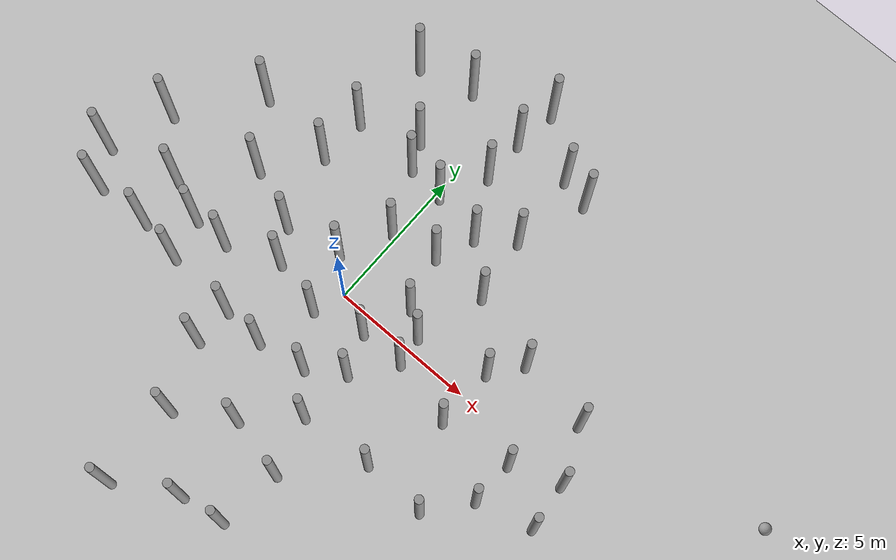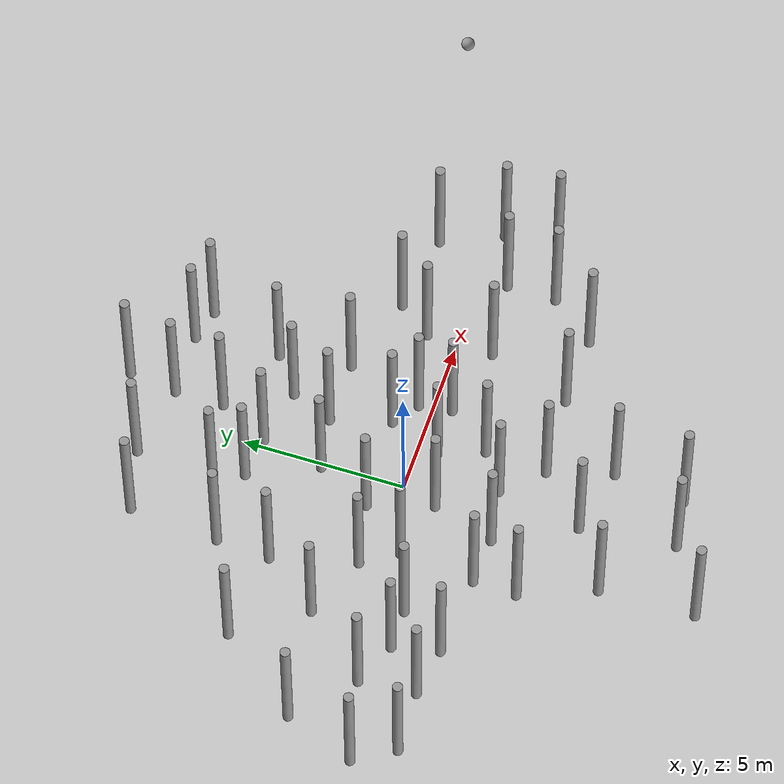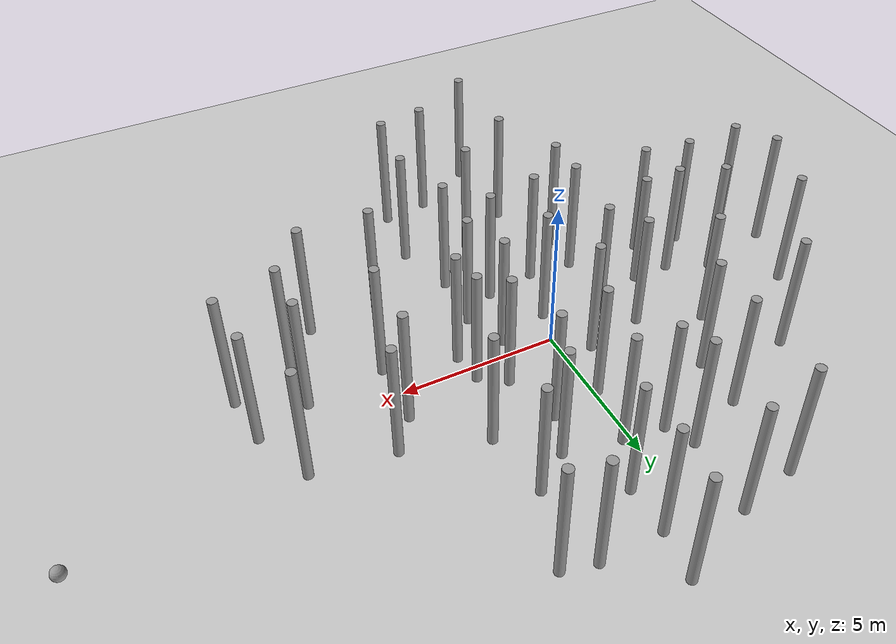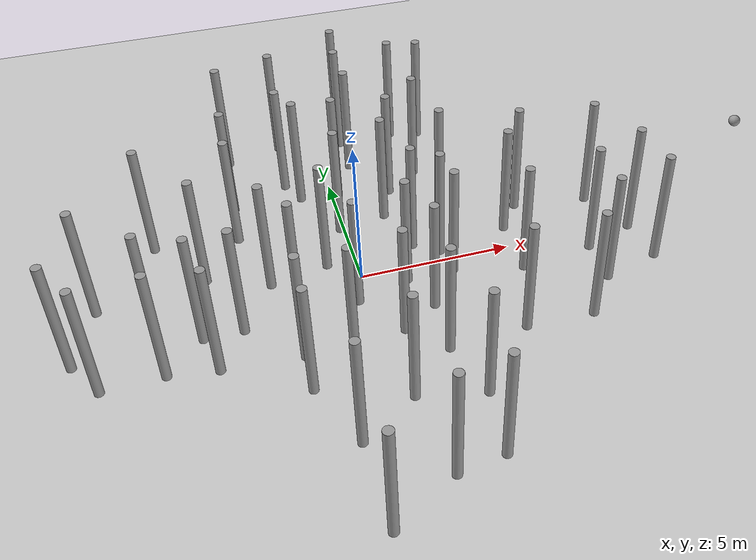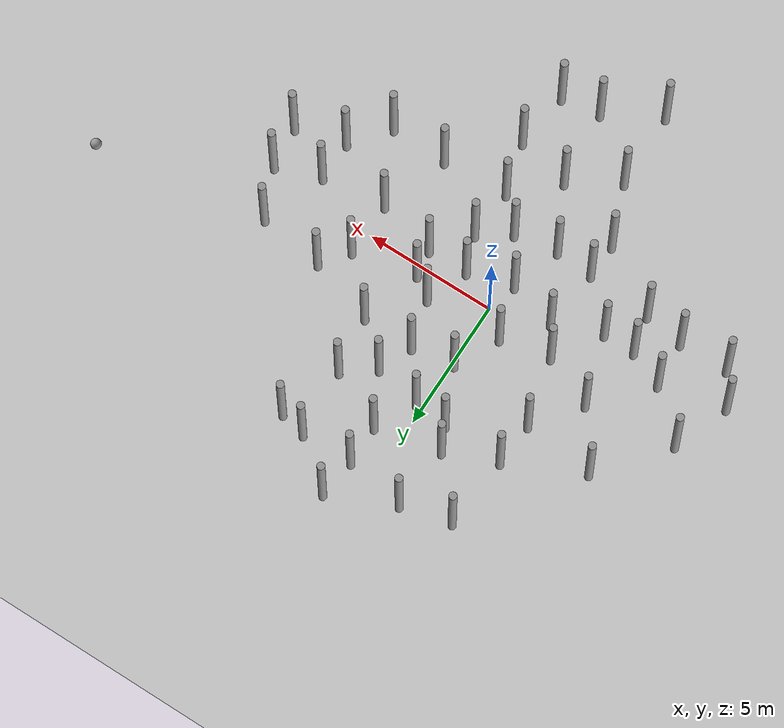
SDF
<sdf version="1.6">
 <world name="default">
  <light name="sun" type="directional">
   <pose>0 0 10 0 -0 0</pose>
   <diffuse>0.8 0.8 0.8 1</diffuse>
   <specular>0.2 0.2 0.2 1</specular>
   <attenuation>
    <range>1000</range>
    <constant>0.9</constant>
    <linear>0.01</linear>
    <quadratic>0.001</quadratic>
   </attenuation>
   <direction>-0.5 0.1 -0.9</direction>
  </light>
  <model name="ground_plane">
   <static>1</static>
   <link name="link">
    <collision name="collision">
     <geometry><plane><normal>0 0 1</normal><size>100 100</size></plane></geometry>
     <surface><friction><ode><mu>100</mu><mu2>50</mu2></ode></friction></surface>
    </collision>
    <visual name="visual">
     <cast_shadows>0</cast_shadows>
     <geometry><plane><normal>0 0 1</normal><size>100 100</size></plane></geometry>
     <material>
      <script><uri>file://media/materials/scripts/gazebo.material</uri><name>Gazebo/Grey</name></script>
     </material>
    </visual>
   </link>
  </model>
  <gravity>0 0 -9.8</gravity>
  <magnetic_field>6e-06 2.3e-05 -4.2e-05</magnetic_field>
  <atmosphere type="adiabatic"/>
  <physics name="default_physics" default="0" type="ode">
   <max_step_size>0.001</max_step_size>
   <real_time_factor>1</real_time_factor>
   <real_time_update_rate>1000</real_time_update_rate>
  </physics>
  <scene><ambient>0.4 0.4 0.4 1</ambient><background>0.7 0.7 0.7 1</background><shadows>1</shadows></scene>
  <spherical_coordinates>
   <surface_model>EARTH_WGS84</surface_model>
   <latitude_deg>0</latitude_deg>
   <longitude_deg>0</longitude_deg>
   <elevation>0</elevation>
   <heading_deg>0</heading_deg>
  </spherical_coordinates>
  <model name="unit_cylinder">
   <link name="link">
    <inertial>
     <mass>1000</mass>
     <inertia><ixx>145.833</ixx><ixy>0</ixy><ixz>0</ixz><iyy>145.833</iyy><iyz>0</iyz><izz>125</izz></inertia>
    </inertial>
    <visual name="visual">
     <geometry><cylinder><radius>0.15</radius><length>4</length></cylinder></geometry>
     <material>
      <script><name>Gazebo/Grey</name><uri>file://media/materials/scripts/gazebo.material</uri></script>
      <shader type="pixel"><normal_map>__default__</normal_map></shader>
      <ambient>0.3 0.3 0.3 1</ambient>
      <diffuse>0.7 0.7 0.7 1</diffuse>
      <specular>0.01 0.01 0.01 1</specular>
      <emissive>0 0 0 1</emissive>
     </material>
    </visual>
    <collision name="collision">
     <geometry><cylinder><radius>0.15</radius><length>4</length></cylinder></geometry>
     <surface>
      <friction>
       <ode><mu>1</mu><mu2>1</mu2><fdir1>0 0 0</fdir1><slip1>0</slip1><slip2>0</slip2></ode>
       <torsional>
        <coefficient>1</coefficient>
        <patch_radius>0</patch_radius>
        <surface_radius>0</surface_radius>
        <use_patch_radius>1</use_patch_radius>
        <ode><slip>0</slip></ode>
       </torsional>
      </friction>
      <bounce><restitution_coefficient>0</restitution_coefficient><threshold>1e+06</threshold></bounce>
      <contact>
       <collide_without_contact>0</collide_without_contact>
       <collide_without_contact_bitmask>1</collide_without_contact_bitmask>
       <collide_bitmask>1</collide_bitmask>
       <ode>
        <soft_cfm>0</soft_cfm>
        <soft_erp>0.2</soft_erp>
        <kp>1e+13</kp>
        <kd>1</kd>
        <max_vel>0.01</max_vel>
        <min_depth>0</min_depth>
       </ode>
       <bullet>
        <split_impulse>1</split_impulse>
        <split_impulse_penetration_threshold>-0.01</split_impulse_penetration_threshold>
        <soft_cfm>0</soft_cfm>
        <soft_erp>0.2</soft_erp>
        <kp>1e+13</kp>
        <kd>1</kd>
       </bullet>
      </contact>
     </surface>
    </collision>
   </link>
   <static>0</static>
   <pose>-2.1717 -0.620709 2 0 0 -0.002853</pose>
  </model>
  <model name="unit_cylinder_clone">
   <link name="link">
    <inertial>
     <mass>1000</mass>
     <inertia><ixx>145.833</ixx><ixy>0</ixy><ixz>0</ixz><iyy>145.833</iyy><iyz>0</iyz><izz>125</izz></inertia>
    </inertial>
    <visual name="visual">
     <geometry><cylinder><radius>0.15</radius><length>4</length></cylinder></geometry>
     <material>
      <script><name>Gazebo/Grey</name><uri>file://media/materials/scripts/gazebo.material</uri></script>
      <shader type="pixel"><normal_map>__default__</normal_map></shader>
      <ambient>0.3 0.3 0.3 1</ambient>
      <diffuse>0.7 0.7 0.7 1</diffuse>
      <specular>0.01 0.01 0.01 1</specular>
      <emissive>0 0 0 1</emissive>
     </material>
    </visual>
    <collision name="collision">
     <geometry><cylinder><radius>0.15</radius><length>4</length></cylinder></geometry>
     <surface>
      <friction>
       <ode><mu>1</mu><mu2>1</mu2><fdir1>0 0 0</fdir1><slip1>0</slip1><slip2>0</slip2></ode>
       <torsional>
        <coefficient>1</coefficient>
        <patch_radius>0</patch_radius>
        <surface_radius>0</surface_radius>
        <use_patch_radius>1</use_patch_radius>
        <ode><slip>0</slip></ode>
       </torsional>
      </friction>
      <bounce><restitution_coefficient>0</restitution_coefficient><threshold>1e+06</threshold></bounce>
      <contact>
       <collide_without_contact>0</collide_without_contact>
       <collide_without_contact_bitmask>1</collide_without_contact_bitmask>
       <collide_bitmask>1</collide_bitmask>
       <ode>
        <soft_cfm>0</soft_cfm>
        <soft_erp>0.2</soft_erp>
        <kp>1e+13</kp>
        <kd>1</kd>
        <max_vel>0.01</max_vel>
        <min_depth>0</min_depth>
       </ode>
       <bullet>
        <split_impulse>1</split_impulse>
        <split_impulse_penetration_threshold>-0.01</split_impulse_penetration_threshold>
        <soft_cfm>0</soft_cfm>
        <soft_erp>0.2</soft_erp>
        <kp>1e+13</kp>
        <kd>1</kd>
       </bullet>
      </contact>
     </surface>
    </collision>
   </link>
   <static>0</static>
   <pose>2.79109 0.434889 1.99999 0 0 -0.002779</pose>
  </model>
  <model name="unit_cylinder_clone_0">
   <link name="link">
    <inertial>
     <mass>1000</mass>
     <inertia><ixx>145.833</ixx><ixy>0</ixy><ixz>0</ixz><iyy>145.833</iyy><iyz>0</iyz><izz>125</izz></inertia>
    </inertial>
    <visual name="visual">
     <geometry><cylinder><radius>0.15</radius><length>4</length></cylinder></geometry>
     <material>
      <script><name>Gazebo/Grey</name><uri>file://media/materials/scripts/gazebo.material</uri></script>
      <shader type="pixel"><normal_map>__default__</normal_map></shader>
      <ambient>0.3 0.3 0.3 1</ambient>
      <diffuse>0.7 0.7 0.7 1</diffuse>
      <specular>0.01 0.01 0.01 1</specular>
      <emissive>0 0 0 1</emissive>
     </material>
    </visual>
    <collision name="collision">
     <geometry><cylinder><radius>0.15</radius><length>4</length></cylinder></geometry>
     <surface>
      <friction>
       <ode><mu>1</mu><mu2>1</mu2><fdir1>0 0 0</fdir1><slip1>0</slip1><slip2>0</slip2></ode>
       <torsional>
        <coefficient>1</coefficient>
        <patch_radius>0</patch_radius>
        <surface_radius>0</surface_radius>
        <use_patch_radius>1</use_patch_radius>
        <ode><slip>0</slip></ode>
       </torsional>
      </friction>
      <bounce><restitution_coefficient>0</restitution_coefficient><threshold>1e+06</threshold></bounce>
      <contact>
       <collide_without_contact>0</collide_without_contact>
       <collide_without_contact_bitmask>1</collide_without_contact_bitmask>
       <collide_bitmask>1</collide_bitmask>
       <ode>
        <soft_cfm>0</soft_cfm>
        <soft_erp>0.2</soft_erp>
        <kp>1e+13</kp>
        <kd>1</kd>
        <max_vel>0.01</max_vel>
        <min_depth>0</min_depth>
       </ode>
       <bullet>
        <split_impulse>1</split_impulse>
        <split_impulse_penetration_threshold>-0.01</split_impulse_penetration_threshold>
        <soft_cfm>0</soft_cfm>
        <soft_erp>0.2</soft_erp>
        <kp>1e+13</kp>
        <kd>1</kd>
       </bullet>
      </contact>
     </surface>
    </collision>
   </link>
   <static>0</static>
   <pose>-0.125925 2.52894 2 0 0 -0.002862</pose>
  </model>
  <model name="unit_cylinder_clone_1">
   <link name="link">
    <inertial>
     <mass>1000</mass>
     <inertia><ixx>145.833</ixx><ixy>0</ixy><ixz>0</ixz><iyy>145.833</iyy><iyz>0</iyz><izz>125</izz></inertia>
    </inertial>
    <visual name="visual">
     <geometry><cylinder><radius>0.15</radius><length>4</length></cylinder></geometry>
     <material>
      <script><name>Gazebo/Grey</name><uri>file://media/materials/scripts/gazebo.material</uri></script>
      <shader type="pixel"><normal_map>__default__</normal_map></shader>
      <ambient>0.3 0.3 0.3 1</ambient>
      <diffuse>0.7 0.7 0.7 1</diffuse>
      <specular>0.01 0.01 0.01 1</specular>
      <emissive>0 0 0 1</emissive>
     </material>
    </visual>
    <collision name="collision">
     <geometry><cylinder><radius>0.15</radius><length>4</length></cylinder></geometry>
     <surface>
      <friction>
       <ode><mu>1</mu><mu2>1</mu2><fdir1>0 0 0</fdir1><slip1>0</slip1><slip2>0</slip2></ode>
       <torsional>
        <coefficient>1</coefficient>
        <patch_radius>0</patch_radius>
        <surface_radius>0</surface_radius>
        <use_patch_radius>1</use_patch_radius>
        <ode><slip>0</slip></ode>
       </torsional>
      </friction>
      <bounce><restitution_coefficient>0</restitution_coefficient><threshold>1e+06</threshold></bounce>
      <contact>
       <collide_without_contact>0</collide_without_contact>
       <collide_without_contact_bitmask>1</collide_without_contact_bitmask>
       <collide_bitmask>1</collide_bitmask>
       <ode>
        <soft_cfm>0</soft_cfm>
        <soft_erp>0.2</soft_erp>
        <kp>1e+13</kp>
        <kd>1</kd>
        <max_vel>0.01</max_vel>
        <min_depth>0</min_depth>
       </ode>
       <bullet>
        <split_impulse>1</split_impulse>
        <split_impulse_penetration_threshold>-0.01</split_impulse_penetration_threshold>
        <soft_cfm>0</soft_cfm>
        <soft_erp>0.2</soft_erp>
        <kp>1e+13</kp>
        <kd>1</kd>
       </bullet>
      </contact>
     </surface>
    </collision>
   </link>
   <static>0</static>
   <pose>1.48887 2.81387 2 0 0 -0.00453</pose>
  </model>
  <model name="unit_cylinder_clone_2">
   <link name="link">
    <inertial>
     <mass>1000</mass>
     <inertia><ixx>145.833</ixx><ixy>0</ixy><ixz>0</ixz><iyy>145.833</iyy><iyz>0</iyz><izz>125</izz></inertia>
    </inertial>
    <visual name="visual">
     <geometry><cylinder><radius>0.15</radius><length>4</length></cylinder></geometry>
     <material>
      <script><name>Gazebo/Grey</name><uri>file://media/materials/scripts/gazebo.material</uri></script>
      <shader type="pixel"><normal_map>__default__</normal_map></shader>
      <ambient>0.3 0.3 0.3 1</ambient>
      <diffuse>0.7 0.7 0.7 1</diffuse>
      <specular>0.01 0.01 0.01 1</specular>
      <emissive>0 0 0 1</emissive>
     </material>
    </visual>
    <collision name="collision">
     <geometry><cylinder><radius>0.15</radius><length>4</length></cylinder></geometry>
     <surface>
      <friction>
       <ode><mu>1</mu><mu2>1</mu2><fdir1>0 0 0</fdir1><slip1>0</slip1><slip2>0</slip2></ode>
       <torsional>
        <coefficient>1</coefficient>
        <patch_radius>0</patch_radius>
        <surface_radius>0</surface_radius>
        <use_patch_radius>1</use_patch_radius>
        <ode><slip>0</slip></ode>
       </torsional>
      </friction>
      <bounce><restitution_coefficient>0</restitution_coefficient><threshold>1e+06</threshold></bounce>
      <contact>
       <collide_without_contact>0</collide_without_contact>
       <collide_without_contact_bitmask>1</collide_without_contact_bitmask>
       <collide_bitmask>1</collide_bitmask>
       <ode>
        <soft_cfm>0</soft_cfm>
        <soft_erp>0.2</soft_erp>
        <kp>1e+13</kp>
        <kd>1</kd>
        <max_vel>0.01</max_vel>
        <min_depth>0</min_depth>
       </ode>
       <bullet>
        <split_impulse>1</split_impulse>
        <split_impulse_penetration_threshold>-0.01</split_impulse_penetration_threshold>
        <soft_cfm>0</soft_cfm>
        <soft_erp>0.2</soft_erp>
        <kp>1e+13</kp>
        <kd>1</kd>
       </bullet>
      </contact>
     </surface>
    </collision>
   </link>
   <static>0</static>
   <pose>-1.07326 4.59014 2 0 0 -0.002941</pose>
  </model>
  <model name="unit_cylinder_clone_3">
   <link name="link">
    <inertial>
     <mass>1000</mass>
     <inertia><ixx>145.833</ixx><ixy>0</ixy><ixz>0</ixz><iyy>145.833</iyy><iyz>0</iyz><izz>125</izz></inertia>
    </inertial>
    <visual name="visual">
     <geometry><cylinder><radius>0.15</radius><length>4</length></cylinder></geometry>
     <material>
      <script><name>Gazebo/Grey</name><uri>file://media/materials/scripts/gazebo.material</uri></script>
      <shader type="pixel"><normal_map>__default__</normal_map></shader>
      <ambient>0.3 0.3 0.3 1</ambient>
      <diffuse>0.7 0.7 0.7 1</diffuse>
      <specular>0.01 0.01 0.01 1</specular>
      <emissive>0 0 0 1</emissive>
     </material>
    </visual>
    <collision name="collision">
     <geometry><cylinder><radius>0.15</radius><length>4</length></cylinder></geometry>
     <surface>
      <friction>
       <ode><mu>1</mu><mu2>1</mu2><fdir1>0 0 0</fdir1><slip1>0</slip1><slip2>0</slip2></ode>
       <torsional>
        <coefficient>1</coefficient>
        <patch_radius>0</patch_radius>
        <surface_radius>0</surface_radius>
        <use_patch_radius>1</use_patch_radius>
        <ode><slip>0</slip></ode>
       </torsional>
      </friction>
      <bounce><restitution_coefficient>0</restitution_coefficient><threshold>1e+06</threshold></bounce>
      <contact>
       <collide_without_contact>0</collide_without_contact>
       <collide_without_contact_bitmask>1</collide_without_contact_bitmask>
       <collide_bitmask>1</collide_bitmask>
       <ode>
        <soft_cfm>0</soft_cfm>
        <soft_erp>0.2</soft_erp>
        <kp>1e+13</kp>
        <kd>1</kd>
        <max_vel>0.01</max_vel>
        <min_depth>0</min_depth>
       </ode>
       <bullet>
        <split_impulse>1</split_impulse>
        <split_impulse_penetration_threshold>-0.01</split_impulse_penetration_threshold>
        <soft_cfm>0</soft_cfm>
        <soft_erp>0.2</soft_erp>
        <kp>1e+13</kp>
        <kd>1</kd>
       </bullet>
      </contact>
     </surface>
    </collision>
   </link>
   <static>0</static>
   <pose>1.00014 6.00017 2 0 0 -0.002932</pose>
  </model>
  <model name="unit_cylinder_clone_4">
   <link name="link">
    <inertial>
     <mass>1000</mass>
     <inertia><ixx>145.833</ixx><ixy>0</ixy><ixz>0</ixz><iyy>145.833</iyy><iyz>0</iyz><izz>125</izz></inertia>
    </inertial>
    <visual name="visual">
     <geometry><cylinder><radius>0.15</radius><length>4</length></cylinder></geometry>
     <material>
      <script><name>Gazebo/Grey</name><uri>file://media/materials/scripts/gazebo.material</uri></script>
      <shader type="pixel"><normal_map>__default__</normal_map></shader>
      <ambient>0.3 0.3 0.3 1</ambient>
      <diffuse>0.7 0.7 0.7 1</diffuse>
      <specular>0.01 0.01 0.01 1</specular>
      <emissive>0 0 0 1</emissive>
     </material>
    </visual>
    <collision name="collision">
     <geometry><cylinder><radius>0.15</radius><length>4</length></cylinder></geometry>
     <surface>
      <friction>
       <ode><mu>1</mu><mu2>1</mu2><fdir1>0 0 0</fdir1><slip1>0</slip1><slip2>0</slip2></ode>
       <torsional>
        <coefficient>1</coefficient>
        <patch_radius>0</patch_radius>
        <surface_radius>0</surface_radius>
        <use_patch_radius>1</use_patch_radius>
        <ode><slip>0</slip></ode>
       </torsional>
      </friction>
      <bounce><restitution_coefficient>0</restitution_coefficient><threshold>1e+06</threshold></bounce>
      <contact>
       <collide_without_contact>0</collide_without_contact>
       <collide_without_contact_bitmask>1</collide_without_contact_bitmask>
       <collide_bitmask>1</collide_bitmask>
       <ode>
        <soft_cfm>0</soft_cfm>
        <soft_erp>0.2</soft_erp>
        <kp>1e+13</kp>
        <kd>1</kd>
        <max_vel>0.01</max_vel>
        <min_depth>0</min_depth>
       </ode>
       <bullet>
        <split_impulse>1</split_impulse>
        <split_impulse_penetration_threshold>-0.01</split_impulse_penetration_threshold>
        <soft_cfm>0</soft_cfm>
        <soft_erp>0.2</soft_erp>
        <kp>1e+13</kp>
        <kd>1</kd>
       </bullet>
      </contact>
     </surface>
    </collision>
   </link>
   <static>0</static>
   <pose>-3.9809 -1.32842 2 0 0 -0.002698</pose>
  </model>
  <model name="unit_cylinder_clone_5">
   <link name="link">
    <inertial>
     <mass>1000</mass>
     <inertia><ixx>145.833</ixx><ixy>0</ixy><ixz>0</ixz><iyy>145.833</iyy><iyz>0</iyz><izz>125</izz></inertia>
    </inertial>
    <visual name="visual">
     <geometry><cylinder><radius>0.15</radius><length>4</length></cylinder></geometry>
     <material>
      <script><name>Gazebo/Grey</name><uri>file://media/materials/scripts/gazebo.material</uri></script>
      <shader type="pixel"><normal_map>__default__</normal_map></shader>
      <ambient>0.3 0.3 0.3 1</ambient>
      <diffuse>0.7 0.7 0.7 1</diffuse>
      <specular>0.01 0.01 0.01 1</specular>
      <emissive>0 0 0 1</emissive>
     </material>
    </visual>
    <collision name="collision">
     <geometry><cylinder><radius>0.15</radius><length>4</length></cylinder></geometry>
     <surface>
      <friction>
       <ode><mu>1</mu><mu2>1</mu2><fdir1>0 0 0</fdir1><slip1>0</slip1><slip2>0</slip2></ode>
       <torsional>
        <coefficient>1</coefficient>
        <patch_radius>0</patch_radius>
        <surface_radius>0</surface_radius>
        <use_patch_radius>1</use_patch_radius>
        <ode><slip>0</slip></ode>
       </torsional>
      </friction>
      <bounce><restitution_coefficient>0</restitution_coefficient><threshold>1e+06</threshold></bounce>
      <contact>
       <collide_without_contact>0</collide_without_contact>
       <collide_without_contact_bitmask>1</collide_without_contact_bitmask>
       <collide_bitmask>1</collide_bitmask>
       <ode>
        <soft_cfm>0</soft_cfm>
        <soft_erp>0.2</soft_erp>
        <kp>1e+13</kp>
        <kd>1</kd>
        <max_vel>0.01</max_vel>
        <min_depth>0</min_depth>
       </ode>
       <bullet>
        <split_impulse>1</split_impulse>
        <split_impulse_penetration_threshold>-0.01</split_impulse_penetration_threshold>
        <soft_cfm>0</soft_cfm>
        <soft_erp>0.2</soft_erp>
        <kp>1e+13</kp>
        <kd>1</kd>
       </bullet>
      </contact>
     </surface>
    </collision>
   </link>
   <static>0</static>
   <pose>-4.81547 1.25343 1.99999 0 0 -0.002692</pose>
  </model>
  <model name="unit_cylinder_clone_6">
   <link name="link">
    <inertial>
     <mass>1000</mass>
     <inertia><ixx>145.833</ixx><ixy>0</ixy><ixz>0</ixz><iyy>145.833</iyy><iyz>0</iyz><izz>125</izz></inertia>
    </inertial>
    <visual name="visual">
     <geometry><cylinder><radius>0.15</radius><length>4</length></cylinder></geometry>
     <material>
      <script><name>Gazebo/Grey</name><uri>file://media/materials/scripts/gazebo.material</uri></script>
      <shader type="pixel"><normal_map>__default__</normal_map></shader>
      <ambient>0.3 0.3 0.3 1</ambient>
      <diffuse>0.7 0.7 0.7 1</diffuse>
      <specular>0.01 0.01 0.01 1</specular>
      <emissive>0 0 0 1</emissive>
     </material>
    </visual>
    <collision name="collision">
     <geometry><cylinder><radius>0.15</radius><length>4</length></cylinder></geometry>
     <surface>
      <friction>
       <ode><mu>1</mu><mu2>1</mu2><fdir1>0 0 0</fdir1><slip1>0</slip1><slip2>0</slip2></ode>
       <torsional>
        <coefficient>1</coefficient>
        <patch_radius>0</patch_radius>
        <surface_radius>0</surface_radius>
        <use_patch_radius>1</use_patch_radius>
        <ode><slip>0</slip></ode>
       </torsional>
      </friction>
      <bounce><restitution_coefficient>0</restitution_coefficient><threshold>1e+06</threshold></bounce>
      <contact>
       <collide_without_contact>0</collide_without_contact>
       <collide_without_contact_bitmask>1</collide_without_contact_bitmask>
       <collide_bitmask>1</collide_bitmask>
       <ode>
        <soft_cfm>0</soft_cfm>
        <soft_erp>0.2</soft_erp>
        <kp>1e+13</kp>
        <kd>1</kd>
        <max_vel>0.01</max_vel>
        <min_depth>0</min_depth>
       </ode>
       <bullet>
        <split_impulse>1</split_impulse>
        <split_impulse_penetration_threshold>-0.01</split_impulse_penetration_threshold>
        <soft_cfm>0</soft_cfm>
        <soft_erp>0.2</soft_erp>
        <kp>1e+13</kp>
        <kd>1</kd>
       </bullet>
      </contact>
     </surface>
    </collision>
   </link>
   <static>0</static>
   <pose>-3.52321 3.00017 2 0 0 -0.002919</pose>
  </model>
  <model name="unit_cylinder_clone_7">
   <link name="link">
    <inertial>
     <mass>1000</mass>
     <inertia><ixx>145.833</ixx><ixy>0</ixy><ixz>0</ixz><iyy>145.833</iyy><iyz>0</iyz><izz>125</izz></inertia>
    </inertial>
    <visual name="visual">
     <geometry><cylinder><radius>0.15</radius><length>4</length></cylinder></geometry>
     <material>
      <script><name>Gazebo/Grey</name><uri>file://media/materials/scripts/gazebo.material</uri></script>
      <shader type="pixel"><normal_map>__default__</normal_map></shader>
      <ambient>0.3 0.3 0.3 1</ambient>
      <diffuse>0.7 0.7 0.7 1</diffuse>
      <specular>0.01 0.01 0.01 1</specular>
      <emissive>0 0 0 1</emissive>
     </material>
    </visual>
    <collision name="collision">
     <geometry><cylinder><radius>0.15</radius><length>4</length></cylinder></geometry>
     <surface>
      <friction>
       <ode><mu>1</mu><mu2>1</mu2><fdir1>0 0 0</fdir1><slip1>0</slip1><slip2>0</slip2></ode>
       <torsional>
        <coefficient>1</coefficient>
        <patch_radius>0</patch_radius>
        <surface_radius>0</surface_radius>
        <use_patch_radius>1</use_patch_radius>
        <ode><slip>0</slip></ode>
       </torsional>
      </friction>
      <bounce><restitution_coefficient>0</restitution_coefficient><threshold>1e+06</threshold></bounce>
      <contact>
       <collide_without_contact>0</collide_without_contact>
       <collide_without_contact_bitmask>1</collide_without_contact_bitmask>
       <collide_bitmask>1</collide_bitmask>
       <ode>
        <soft_cfm>0</soft_cfm>
        <soft_erp>0.2</soft_erp>
        <kp>1e+13</kp>
        <kd>1</kd>
        <max_vel>0.01</max_vel>
        <min_depth>0</min_depth>
       </ode>
       <bullet>
        <split_impulse>1</split_impulse>
        <split_impulse_penetration_threshold>-0.01</split_impulse_penetration_threshold>
        <soft_cfm>0</soft_cfm>
        <soft_erp>0.2</soft_erp>
        <kp>1e+13</kp>
        <kd>1</kd>
       </bullet>
      </contact>
     </surface>
    </collision>
   </link>
   <static>0</static>
   <pose>-2.39989 -2.93188 2 0 0 -0.002818</pose>
  </model>
  <model name="unit_cylinder_clone_8">
   <link name="link">
    <inertial>
     <mass>1000</mass>
     <inertia><ixx>145.833</ixx><ixy>0</ixy><ixz>0</ixz><iyy>145.833</iyy><iyz>0</iyz><izz>125</izz></inertia>
    </inertial>
    <visual name="visual">
     <geometry><cylinder><radius>0.15</radius><length>4</length></cylinder></geometry>
     <material>
      <script><name>Gazebo/Grey</name><uri>file://media/materials/scripts/gazebo.material</uri></script>
      <shader type="pixel"><normal_map>__default__</normal_map></shader>
      <ambient>0.3 0.3 0.3 1</ambient>
      <diffuse>0.7 0.7 0.7 1</diffuse>
      <specular>0.01 0.01 0.01 1</specular>
      <emissive>0 0 0 1</emissive>
     </material>
    </visual>
    <collision name="collision">
     <geometry><cylinder><radius>0.15</radius><length>4</length></cylinder></geometry>
     <surface>
      <friction>
       <ode><mu>1</mu><mu2>1</mu2><fdir1>0 0 0</fdir1><slip1>0</slip1><slip2>0</slip2></ode>
       <torsional>
        <coefficient>1</coefficient>
        <patch_radius>0</patch_radius>
        <surface_radius>0</surface_radius>
        <use_patch_radius>1</use_patch_radius>
        <ode><slip>0</slip></ode>
       </torsional>
      </friction>
      <bounce><restitution_coefficient>0</restitution_coefficient><threshold>1e+06</threshold></bounce>
      <contact>
       <collide_without_contact>0</collide_without_contact>
       <collide_without_contact_bitmask>1</collide_without_contact_bitmask>
       <collide_bitmask>1</collide_bitmask>
       <ode>
        <soft_cfm>0</soft_cfm>
        <soft_erp>0.2</soft_erp>
        <kp>1e+13</kp>
        <kd>1</kd>
        <max_vel>0.01</max_vel>
        <min_depth>0</min_depth>
       </ode>
       <bullet>
        <split_impulse>1</split_impulse>
        <split_impulse_penetration_threshold>-0.01</split_impulse_penetration_threshold>
        <soft_cfm>0</soft_cfm>
        <soft_erp>0.2</soft_erp>
        <kp>1e+13</kp>
        <kd>1</kd>
       </bullet>
      </contact>
     </surface>
    </collision>
   </link>
   <static>0</static>
   <pose>-2.85607 0.444434 2 0 0 -0.002866</pose>
  </model>
  <model name="unit_cylinder_clone_10">
   <link name="link">
    <inertial>
     <mass>1000</mass>
     <inertia><ixx>145.833</ixx><ixy>0</ixy><ixz>0</ixz><iyy>145.833</iyy><iyz>0</iyz><izz>125</izz></inertia>
    </inertial>
    <visual name="visual">
     <geometry><cylinder><radius>0.15</radius><length>4</length></cylinder></geometry>
     <material>
      <script><name>Gazebo/Grey</name><uri>file://media/materials/scripts/gazebo.material</uri></script>
      <shader type="pixel"><normal_map>__default__</normal_map></shader>
      <ambient>0.3 0.3 0.3 1</ambient>
      <diffuse>0.7 0.7 0.7 1</diffuse>
      <specular>0.01 0.01 0.01 1</specular>
      <emissive>0 0 0 1</emissive>
     </material>
    </visual>
    <collision name="collision">
     <geometry><cylinder><radius>0.15</radius><length>4</length></cylinder></geometry>
     <surface>
      <friction>
       <ode><mu>1</mu><mu2>1</mu2><fdir1>0 0 0</fdir1><slip1>0</slip1><slip2>0</slip2></ode>
       <torsional>
        <coefficient>1</coefficient>
        <patch_radius>0</patch_radius>
        <surface_radius>0</surface_radius>
        <use_patch_radius>1</use_patch_radius>
        <ode><slip>0</slip></ode>
       </torsional>
      </friction>
      <bounce><restitution_coefficient>0</restitution_coefficient><threshold>1e+06</threshold></bounce>
      <contact>
       <collide_without_contact>0</collide_without_contact>
       <collide_without_contact_bitmask>1</collide_without_contact_bitmask>
       <collide_bitmask>1</collide_bitmask>
       <ode>
        <soft_cfm>0</soft_cfm>
        <soft_erp>0.2</soft_erp>
        <kp>1e+13</kp>
        <kd>1</kd>
        <max_vel>0.01</max_vel>
        <min_depth>0</min_depth>
       </ode>
       <bullet>
        <split_impulse>1</split_impulse>
        <split_impulse_penetration_threshold>-0.01</split_impulse_penetration_threshold>
        <soft_cfm>0</soft_cfm>
        <soft_erp>0.2</soft_erp>
        <kp>1e+13</kp>
        <kd>1</kd>
       </bullet>
      </contact>
     </surface>
    </collision>
   </link>
   <static>0</static>
   <pose>-6.42357 -2.50125 2 0 0 -0.002756</pose>
  </model>
  <model name="unit_cylinder_clone_11">
   <link name="link">
    <inertial>
     <mass>1000</mass>
     <inertia><ixx>145.833</ixx><ixy>0</ixy><ixz>0</ixz><iyy>145.833</iyy><iyz>0</iyz><izz>125</izz></inertia>
    </inertial>
    <visual name="visual">
     <geometry><cylinder><radius>0.15</radius><length>4</length></cylinder></geometry>
     <material>
      <script><name>Gazebo/Grey</name><uri>file://media/materials/scripts/gazebo.material</uri></script>
      <shader type="pixel"><normal_map>__default__</normal_map></shader>
      <ambient>0.3 0.3 0.3 1</ambient>
      <diffuse>0.7 0.7 0.7 1</diffuse>
      <specular>0.01 0.01 0.01 1</specular>
      <emissive>0 0 0 1</emissive>
     </material>
    </visual>
    <collision name="collision">
     <geometry><cylinder><radius>0.15</radius><length>4</length></cylinder></geometry>
     <surface>
      <friction>
       <ode><mu>1</mu><mu2>1</mu2><fdir1>0 0 0</fdir1><slip1>0</slip1><slip2>0</slip2></ode>
       <torsional>
        <coefficient>1</coefficient>
        <patch_radius>0</patch_radius>
        <surface_radius>0</surface_radius>
        <use_patch_radius>1</use_patch_radius>
        <ode><slip>0</slip></ode>
       </torsional>
      </friction>
      <bounce><restitution_coefficient>0</restitution_coefficient><threshold>1e+06</threshold></bounce>
      <contact>
       <collide_without_contact>0</collide_without_contact>
       <collide_without_contact_bitmask>1</collide_without_contact_bitmask>
       <collide_bitmask>1</collide_bitmask>
       <ode>
        <soft_cfm>0</soft_cfm>
        <soft_erp>0.2</soft_erp>
        <kp>1e+13</kp>
        <kd>1</kd>
        <max_vel>0.01</max_vel>
        <min_depth>0</min_depth>
       </ode>
       <bullet>
        <split_impulse>1</split_impulse>
        <split_impulse_penetration_threshold>-0.01</split_impulse_penetration_threshold>
        <soft_cfm>0</soft_cfm>
        <soft_erp>0.2</soft_erp>
        <kp>1e+13</kp>
        <kd>1</kd>
       </bullet>
      </contact>
     </surface>
    </collision>
   </link>
   <static>0</static>
   <pose>-4.89753 -2.73769 2 0 0 -0.002756</pose>
  </model>
  <model name="unit_cylinder_clone_13">
   <link name="link">
    <inertial>
     <mass>1000</mass>
     <inertia><ixx>145.833</ixx><ixy>0</ixy><ixz>0</ixz><iyy>145.833</iyy><iyz>0</iyz><izz>125</izz></inertia>
    </inertial>
    <visual name="visual">
     <geometry><cylinder><radius>0.15</radius><length>4</length></cylinder></geometry>
     <material>
      <script><name>Gazebo/Grey</name><uri>file://media/materials/scripts/gazebo.material</uri></script>
      <shader type="pixel"><normal_map>__default__</normal_map></shader>
      <ambient>0.3 0.3 0.3 1</ambient>
      <diffuse>0.7 0.7 0.7 1</diffuse>
      <specular>0.01 0.01 0.01 1</specular>
      <emissive>0 0 0 1</emissive>
     </material>
    </visual>
    <collision name="collision">
     <geometry><cylinder><radius>0.15</radius><length>4</length></cylinder></geometry>
     <surface>
      <friction>
       <ode><mu>1</mu><mu2>1</mu2><fdir1>0 0 0</fdir1><slip1>0</slip1><slip2>0</slip2></ode>
       <torsional>
        <coefficient>1</coefficient>
        <patch_radius>0</patch_radius>
        <surface_radius>0</surface_radius>
        <use_patch_radius>1</use_patch_radius>
        <ode><slip>0</slip></ode>
       </torsional>
      </friction>
      <bounce><restitution_coefficient>0</restitution_coefficient><threshold>1e+06</threshold></bounce>
      <contact>
       <collide_without_contact>0</collide_without_contact>
       <collide_without_contact_bitmask>1</collide_without_contact_bitmask>
       <collide_bitmask>1</collide_bitmask>
       <ode>
        <soft_cfm>0</soft_cfm>
        <soft_erp>0.2</soft_erp>
        <kp>1e+13</kp>
        <kd>1</kd>
        <max_vel>0.01</max_vel>
        <min_depth>0</min_depth>
       </ode>
       <bullet>
        <split_impulse>1</split_impulse>
        <split_impulse_penetration_threshold>-0.01</split_impulse_penetration_threshold>
        <soft_cfm>0</soft_cfm>
        <soft_erp>0.2</soft_erp>
        <kp>1e+13</kp>
        <kd>1</kd>
       </bullet>
      </contact>
     </surface>
    </collision>
   </link>
   <static>0</static>
   <pose>-5.21821 -1.32978 1.99999 0 0 -0.002718</pose>
  </model>
  <model name="unit_cylinder_clone_14">
   <link name="link">
    <inertial>
     <mass>1000</mass>
     <inertia><ixx>145.833</ixx><ixy>0</ixy><ixz>0</ixz><iyy>145.833</iyy><iyz>0</iyz><izz>125</izz></inertia>
    </inertial>
    <visual name="visual">
     <geometry><cylinder><radius>0.15</radius><length>4</length></cylinder></geometry>
     <material>
      <script><name>Gazebo/Grey</name><uri>file://media/materials/scripts/gazebo.material</uri></script>
      <shader type="pixel"><normal_map>__default__</normal_map></shader>
      <ambient>0.3 0.3 0.3 1</ambient>
      <diffuse>0.7 0.7 0.7 1</diffuse>
      <specular>0.01 0.01 0.01 1</specular>
      <emissive>0 0 0 1</emissive>
     </material>
    </visual>
    <collision name="collision">
     <geometry><cylinder><radius>0.15</radius><length>4</length></cylinder></geometry>
     <surface>
      <friction>
       <ode><mu>1</mu><mu2>1</mu2><fdir1>0 0 0</fdir1><slip1>0</slip1><slip2>0</slip2></ode>
       <torsional>
        <coefficient>1</coefficient>
        <patch_radius>0</patch_radius>
        <surface_radius>0</surface_radius>
        <use_patch_radius>1</use_patch_radius>
        <ode><slip>0</slip></ode>
       </torsional>
      </friction>
      <bounce><restitution_coefficient>0</restitution_coefficient><threshold>1e+06</threshold></bounce>
      <contact>
       <collide_without_contact>0</collide_without_contact>
       <collide_without_contact_bitmask>1</collide_without_contact_bitmask>
       <collide_bitmask>1</collide_bitmask>
       <ode>
        <soft_cfm>0</soft_cfm>
        <soft_erp>0.2</soft_erp>
        <kp>1e+13</kp>
        <kd>1</kd>
        <max_vel>0.01</max_vel>
        <min_depth>0</min_depth>
       </ode>
       <bullet>
        <split_impulse>1</split_impulse>
        <split_impulse_penetration_threshold>-0.01</split_impulse_penetration_threshold>
        <soft_cfm>0</soft_cfm>
        <soft_erp>0.2</soft_erp>
        <kp>1e+13</kp>
        <kd>1</kd>
       </bullet>
      </contact>
     </surface>
    </collision>
   </link>
   <static>0</static>
   <pose>-6.57283 -0.768217 2 0 0 -0.003051</pose>
  </model>
  <model name="unit_cylinder_clone_15">
   <link name="link">
    <inertial>
     <mass>1000</mass>
     <inertia><ixx>145.833</ixx><ixy>0</ixy><ixz>0</ixz><iyy>145.833</iyy><iyz>0</iyz><izz>125</izz></inertia>
    </inertial>
    <visual name="visual">
     <geometry><cylinder><radius>0.15</radius><length>4</length></cylinder></geometry>
     <material>
      <script><name>Gazebo/Grey</name><uri>file://media/materials/scripts/gazebo.material</uri></script>
      <shader type="pixel"><normal_map>__default__</normal_map></shader>
      <ambient>0.3 0.3 0.3 1</ambient>
      <diffuse>0.7 0.7 0.7 1</diffuse>
      <specular>0.01 0.01 0.01 1</specular>
      <emissive>0 0 0 1</emissive>
     </material>
    </visual>
    <collision name="collision">
     <geometry><cylinder><radius>0.15</radius><length>4</length></cylinder></geometry>
     <surface>
      <friction>
       <ode><mu>1</mu><mu2>1</mu2><fdir1>0 0 0</fdir1><slip1>0</slip1><slip2>0</slip2></ode>
       <torsional>
        <coefficient>1</coefficient>
        <patch_radius>0</patch_radius>
        <surface_radius>0</surface_radius>
        <use_patch_radius>1</use_patch_radius>
        <ode><slip>0</slip></ode>
       </torsional>
      </friction>
      <bounce><restitution_coefficient>0</restitution_coefficient><threshold>1e+06</threshold></bounce>
      <contact>
       <collide_without_contact>0</collide_without_contact>
       <collide_without_contact_bitmask>1</collide_without_contact_bitmask>
       <collide_bitmask>1</collide_bitmask>
       <ode>
        <soft_cfm>0</soft_cfm>
        <soft_erp>0.2</soft_erp>
        <kp>1e+13</kp>
        <kd>1</kd>
        <max_vel>0.01</max_vel>
        <min_depth>0</min_depth>
       </ode>
       <bullet>
        <split_impulse>1</split_impulse>
        <split_impulse_penetration_threshold>-0.01</split_impulse_penetration_threshold>
        <soft_cfm>0</soft_cfm>
        <soft_erp>0.2</soft_erp>
        <kp>1e+13</kp>
        <kd>1</kd>
       </bullet>
      </contact>
     </surface>
    </collision>
   </link>
   <static>0</static>
   <pose>-8.32866 -2.56412 1.99999 0 0 -0.002834</pose>
  </model>
  <model name="unit_cylinder_clone_16">
   <link name="link">
    <inertial>
     <mass>1000</mass>
     <inertia><ixx>145.833</ixx><ixy>0</ixy><ixz>0</ixz><iyy>145.833</iyy><iyz>0</iyz><izz>125</izz></inertia>
    </inertial>
    <visual name="visual">
     <geometry><cylinder><radius>0.15</radius><length>4</length></cylinder></geometry>
     <material>
      <script><name>Gazebo/Grey</name><uri>file://media/materials/scripts/gazebo.material</uri></script>
      <shader type="pixel"><normal_map>__default__</normal_map></shader>
      <ambient>0.3 0.3 0.3 1</ambient>
      <diffuse>0.7 0.7 0.7 1</diffuse>
      <specular>0.01 0.01 0.01 1</specular>
      <emissive>0 0 0 1</emissive>
     </material>
    </visual>
    <collision name="collision">
     <geometry><cylinder><radius>0.15</radius><length>4</length></cylinder></geometry>
     <surface>
      <friction>
       <ode><mu>1</mu><mu2>1</mu2><fdir1>0 0 0</fdir1><slip1>0</slip1><slip2>0</slip2></ode>
       <torsional>
        <coefficient>1</coefficient>
        <patch_radius>0</patch_radius>
        <surface_radius>0</surface_radius>
        <use_patch_radius>1</use_patch_radius>
        <ode><slip>0</slip></ode>
       </torsional>
      </friction>
      <bounce><restitution_coefficient>0</restitution_coefficient><threshold>1e+06</threshold></bounce>
      <contact>
       <collide_without_contact>0</collide_without_contact>
       <collide_without_contact_bitmask>1</collide_without_contact_bitmask>
       <collide_bitmask>1</collide_bitmask>
       <ode>
        <soft_cfm>0</soft_cfm>
        <soft_erp>0.2</soft_erp>
        <kp>1e+13</kp>
        <kd>1</kd>
        <max_vel>0.01</max_vel>
        <min_depth>0</min_depth>
       </ode>
       <bullet>
        <split_impulse>1</split_impulse>
        <split_impulse_penetration_threshold>-0.01</split_impulse_penetration_threshold>
        <soft_cfm>0</soft_cfm>
        <soft_erp>0.2</soft_erp>
        <kp>1e+13</kp>
        <kd>1</kd>
       </bullet>
      </contact>
     </surface>
    </collision>
   </link>
   <static>0</static>
   <pose>-9.06624 -1.36021 1.99999 0 0 -0.002786</pose>
  </model>
  <model name="unit_cylinder_clone_17">
   <link name="link">
    <inertial>
     <mass>1000</mass>
     <inertia><ixx>145.833</ixx><ixy>0</ixy><ixz>0</ixz><iyy>145.833</iyy><iyz>0</iyz><izz>125</izz></inertia>
    </inertial>
    <visual name="visual">
     <geometry><cylinder><radius>0.15</radius><length>4</length></cylinder></geometry>
     <material>
      <script><name>Gazebo/Grey</name><uri>file://media/materials/scripts/gazebo.material</uri></script>
      <shader type="pixel"><normal_map>__default__</normal_map></shader>
      <ambient>0.3 0.3 0.3 1</ambient>
      <diffuse>0.7 0.7 0.7 1</diffuse>
      <specular>0.01 0.01 0.01 1</specular>
      <emissive>0 0 0 1</emissive>
     </material>
    </visual>
    <collision name="collision">
     <geometry><cylinder><radius>0.15</radius><length>4</length></cylinder></geometry>
     <surface>
      <friction>
       <ode><mu>1</mu><mu2>1</mu2><fdir1>0 0 0</fdir1><slip1>0</slip1><slip2>0</slip2></ode>
       <torsional>
        <coefficient>1</coefficient>
        <patch_radius>0</patch_radius>
        <surface_radius>0</surface_radius>
        <use_patch_radius>1</use_patch_radius>
        <ode><slip>0</slip></ode>
       </torsional>
      </friction>
      <bounce><restitution_coefficient>0</restitution_coefficient><threshold>1e+06</threshold></bounce>
      <contact>
       <collide_without_contact>0</collide_without_contact>
       <collide_without_contact_bitmask>1</collide_without_contact_bitmask>
       <collide_bitmask>1</collide_bitmask>
       <ode>
        <soft_cfm>0</soft_cfm>
        <soft_erp>0.2</soft_erp>
        <kp>1e+13</kp>
        <kd>1</kd>
        <max_vel>0.01</max_vel>
        <min_depth>0</min_depth>
       </ode>
       <bullet>
        <split_impulse>1</split_impulse>
        <split_impulse_penetration_threshold>-0.01</split_impulse_penetration_threshold>
        <soft_cfm>0</soft_cfm>
        <soft_erp>0.2</soft_erp>
        <kp>1e+13</kp>
        <kd>1</kd>
       </bullet>
      </contact>
     </surface>
    </collision>
   </link>
   <static>0</static>
   <pose>-8.26971 0.791684 2 0 0 -0.002864</pose>
  </model>
  <model name="unit_cylinder_clone_18">
   <link name="link">
    <inertial>
     <mass>1000</mass>
     <inertia><ixx>145.833</ixx><ixy>0</ixy><ixz>0</ixz><iyy>145.833</iyy><iyz>0</iyz><izz>125</izz></inertia>
    </inertial>
    <visual name="visual">
     <geometry><cylinder><radius>0.15</radius><length>4</length></cylinder></geometry>
     <material>
      <script><name>Gazebo/Grey</name><uri>file://media/materials/scripts/gazebo.material</uri></script>
      <shader type="pixel"><normal_map>__default__</normal_map></shader>
      <ambient>0.3 0.3 0.3 1</ambient>
      <diffuse>0.7 0.7 0.7 1</diffuse>
      <specular>0.01 0.01 0.01 1</specular>
      <emissive>0 0 0 1</emissive>
     </material>
    </visual>
    <collision name="collision">
     <geometry><cylinder><radius>0.15</radius><length>4</length></cylinder></geometry>
     <surface>
      <friction>
       <ode><mu>1</mu><mu2>1</mu2><fdir1>0 0 0</fdir1><slip1>0</slip1><slip2>0</slip2></ode>
       <torsional>
        <coefficient>1</coefficient>
        <patch_radius>0</patch_radius>
        <surface_radius>0</surface_radius>
        <use_patch_radius>1</use_patch_radius>
        <ode><slip>0</slip></ode>
       </torsional>
      </friction>
      <bounce><restitution_coefficient>0</restitution_coefficient><threshold>1e+06</threshold></bounce>
      <contact>
       <collide_without_contact>0</collide_without_contact>
       <collide_without_contact_bitmask>1</collide_without_contact_bitmask>
       <collide_bitmask>1</collide_bitmask>
       <ode>
        <soft_cfm>0</soft_cfm>
        <soft_erp>0.2</soft_erp>
        <kp>1e+13</kp>
        <kd>1</kd>
        <max_vel>0.01</max_vel>
        <min_depth>0</min_depth>
       </ode>
       <bullet>
        <split_impulse>1</split_impulse>
        <split_impulse_penetration_threshold>-0.01</split_impulse_penetration_threshold>
        <soft_cfm>0</soft_cfm>
        <soft_erp>0.2</soft_erp>
        <kp>1e+13</kp>
        <kd>1</kd>
       </bullet>
      </contact>
     </surface>
    </collision>
   </link>
   <static>0</static>
   <pose>1.18456 9.01145 1.99999 0 0 -0.002782</pose>
  </model>
  <model name="unit_cylinder_clone_19">
   <link name="link">
    <inertial>
     <mass>1000</mass>
     <inertia><ixx>145.833</ixx><ixy>0</ixy><ixz>0</ixz><iyy>145.833</iyy><iyz>0</iyz><izz>125</izz></inertia>
    </inertial>
    <visual name="visual">
     <geometry><cylinder><radius>0.15</radius><length>4</length></cylinder></geometry>
     <material>
      <script><name>Gazebo/Grey</name><uri>file://media/materials/scripts/gazebo.material</uri></script>
      <shader type="pixel"><normal_map>__default__</normal_map></shader>
      <ambient>0.3 0.3 0.3 1</ambient>
      <diffuse>0.7 0.7 0.7 1</diffuse>
      <specular>0.01 0.01 0.01 1</specular>
      <emissive>0 0 0 1</emissive>
     </material>
    </visual>
    <collision name="collision">
     <geometry><cylinder><radius>0.15</radius><length>4</length></cylinder></geometry>
     <surface>
      <friction>
       <ode><mu>1</mu><mu2>1</mu2><fdir1>0 0 0</fdir1><slip1>0</slip1><slip2>0</slip2></ode>
       <torsional>
        <coefficient>1</coefficient>
        <patch_radius>0</patch_radius>
        <surface_radius>0</surface_radius>
        <use_patch_radius>1</use_patch_radius>
        <ode><slip>0</slip></ode>
       </torsional>
      </friction>
      <bounce><restitution_coefficient>0</restitution_coefficient><threshold>1e+06</threshold></bounce>
      <contact>
       <collide_without_contact>0</collide_without_contact>
       <collide_without_contact_bitmask>1</collide_without_contact_bitmask>
       <collide_bitmask>1</collide_bitmask>
       <ode>
        <soft_cfm>0</soft_cfm>
        <soft_erp>0.2</soft_erp>
        <kp>1e+13</kp>
        <kd>1</kd>
        <max_vel>0.01</max_vel>
        <min_depth>0</min_depth>
       </ode>
       <bullet>
        <split_impulse>1</split_impulse>
        <split_impulse_penetration_threshold>-0.01</split_impulse_penetration_threshold>
        <soft_cfm>0</soft_cfm>
        <soft_erp>0.2</soft_erp>
        <kp>1e+13</kp>
        <kd>1</kd>
       </bullet>
      </contact>
     </surface>
    </collision>
   </link>
   <static>0</static>
   <pose>-3.20756 7.43044 2 0 0 -0.003296</pose>
  </model>
  <model name="unit_cylinder_clone_20">
   <link name="link">
    <inertial>
     <mass>1000</mass>
     <inertia><ixx>145.833</ixx><ixy>0</ixy><ixz>0</ixz><iyy>145.833</iyy><iyz>0</iyz><izz>125</izz></inertia>
    </inertial>
    <visual name="visual">
     <geometry><cylinder><radius>0.15</radius><length>4</length></cylinder></geometry>
     <material>
      <script><name>Gazebo/Grey</name><uri>file://media/materials/scripts/gazebo.material</uri></script>
      <shader type="pixel"><normal_map>__default__</normal_map></shader>
      <ambient>0.3 0.3 0.3 1</ambient>
      <diffuse>0.7 0.7 0.7 1</diffuse>
      <specular>0.01 0.01 0.01 1</specular>
      <emissive>0 0 0 1</emissive>
     </material>
    </visual>
    <collision name="collision">
     <geometry><cylinder><radius>0.15</radius><length>4</length></cylinder></geometry>
     <surface>
      <friction>
       <ode><mu>1</mu><mu2>1</mu2><fdir1>0 0 0</fdir1><slip1>0</slip1><slip2>0</slip2></ode>
       <torsional>
        <coefficient>1</coefficient>
        <patch_radius>0</patch_radius>
        <surface_radius>0</surface_radius>
        <use_patch_radius>1</use_patch_radius>
        <ode><slip>0</slip></ode>
       </torsional>
      </friction>
      <bounce><restitution_coefficient>0</restitution_coefficient><threshold>1e+06</threshold></bounce>
      <contact>
       <collide_without_contact>0</collide_without_contact>
       <collide_without_contact_bitmask>1</collide_without_contact_bitmask>
       <collide_bitmask>1</collide_bitmask>
       <ode>
        <soft_cfm>0</soft_cfm>
        <soft_erp>0.2</soft_erp>
        <kp>1e+13</kp>
        <kd>1</kd>
        <max_vel>0.01</max_vel>
        <min_depth>0</min_depth>
       </ode>
       <bullet>
        <split_impulse>1</split_impulse>
        <split_impulse_penetration_threshold>-0.01</split_impulse_penetration_threshold>
        <soft_cfm>0</soft_cfm>
        <soft_erp>0.2</soft_erp>
        <kp>1e+13</kp>
        <kd>1</kd>
       </bullet>
      </contact>
     </surface>
    </collision>
   </link>
   <static>0</static>
   <pose>3.98043 7.3233 2 0 0 -0.002803</pose>
  </model>
  <model name="unit_cylinder_clone_21">
   <link name="link">
    <inertial>
     <mass>1000</mass>
     <inertia><ixx>145.833</ixx><ixy>0</ixy><ixz>0</ixz><iyy>145.833</iyy><iyz>0</iyz><izz>125</izz></inertia>
    </inertial>
    <visual name="visual">
     <geometry><cylinder><radius>0.15</radius><length>4</length></cylinder></geometry>
     <material>
      <script><name>Gazebo/Grey</name><uri>file://media/materials/scripts/gazebo.material</uri></script>
      <shader type="pixel"><normal_map>__default__</normal_map></shader>
      <ambient>0.3 0.3 0.3 1</ambient>
      <diffuse>0.7 0.7 0.7 1</diffuse>
      <specular>0.01 0.01 0.01 1</specular>
      <emissive>0 0 0 1</emissive>
     </material>
    </visual>
    <collision name="collision">
     <geometry><cylinder><radius>0.15</radius><length>4</length></cylinder></geometry>
     <surface>
      <friction>
       <ode><mu>1</mu><mu2>1</mu2><fdir1>0 0 0</fdir1><slip1>0</slip1><slip2>0</slip2></ode>
       <torsional>
        <coefficient>1</coefficient>
        <patch_radius>0</patch_radius>
        <surface_radius>0</surface_radius>
        <use_patch_radius>1</use_patch_radius>
        <ode><slip>0</slip></ode>
       </torsional>
      </friction>
      <bounce><restitution_coefficient>0</restitution_coefficient><threshold>1e+06</threshold></bounce>
      <contact>
       <collide_without_contact>0</collide_without_contact>
       <collide_without_contact_bitmask>1</collide_without_contact_bitmask>
       <collide_bitmask>1</collide_bitmask>
       <ode>
        <soft_cfm>0</soft_cfm>
        <soft_erp>0.2</soft_erp>
        <kp>1e+13</kp>
        <kd>1</kd>
        <max_vel>0.01</max_vel>
        <min_depth>0</min_depth>
       </ode>
       <bullet>
        <split_impulse>1</split_impulse>
        <split_impulse_penetration_threshold>-0.01</split_impulse_penetration_threshold>
        <soft_cfm>0</soft_cfm>
        <soft_erp>0.2</soft_erp>
        <kp>1e+13</kp>
        <kd>1</kd>
       </bullet>
      </contact>
     </surface>
    </collision>
   </link>
   <static>0</static>
   <pose>-1.30179 7.90809 2 0 0 -0.005046</pose>
  </model>
  <model name="unit_cylinder_clone_22">
   <link name="link">
    <inertial>
     <mass>1000</mass>
     <inertia><ixx>145.833</ixx><ixy>0</ixy><ixz>0</ixz><iyy>145.833</iyy><iyz>0</iyz><izz>125</izz></inertia>
    </inertial>
    <visual name="visual">
     <geometry><cylinder><radius>0.15</radius><length>4</length></cylinder></geometry>
     <material>
      <script><name>Gazebo/Grey</name><uri>file://media/materials/scripts/gazebo.material</uri></script>
      <shader type="pixel"><normal_map>__default__</normal_map></shader>
      <ambient>0.3 0.3 0.3 1</ambient>
      <diffuse>0.7 0.7 0.7 1</diffuse>
      <specular>0.01 0.01 0.01 1</specular>
      <emissive>0 0 0 1</emissive>
     </material>
    </visual>
    <collision name="collision">
     <geometry><cylinder><radius>0.15</radius><length>4</length></cylinder></geometry>
     <surface>
      <friction>
       <ode><mu>1</mu><mu2>1</mu2><fdir1>0 0 0</fdir1><slip1>0</slip1><slip2>0</slip2></ode>
       <torsional>
        <coefficient>1</coefficient>
        <patch_radius>0</patch_radius>
        <surface_radius>0</surface_radius>
        <use_patch_radius>1</use_patch_radius>
        <ode><slip>0</slip></ode>
       </torsional>
      </friction>
      <bounce><restitution_coefficient>0</restitution_coefficient><threshold>1e+06</threshold></bounce>
      <contact>
       <collide_without_contact>0</collide_without_contact>
       <collide_without_contact_bitmask>1</collide_without_contact_bitmask>
       <collide_bitmask>1</collide_bitmask>
       <ode>
        <soft_cfm>0</soft_cfm>
        <soft_erp>0.2</soft_erp>
        <kp>1e+13</kp>
        <kd>1</kd>
        <max_vel>0.01</max_vel>
        <min_depth>0</min_depth>
       </ode>
       <bullet>
        <split_impulse>1</split_impulse>
        <split_impulse_penetration_threshold>-0.01</split_impulse_penetration_threshold>
        <soft_cfm>0</soft_cfm>
        <soft_erp>0.2</soft_erp>
        <kp>1e+13</kp>
        <kd>1</kd>
       </bullet>
      </contact>
     </surface>
    </collision>
   </link>
   <static>0</static>
   <pose>0.989296 7.51338 1.99999 0 0 -0.002957</pose>
  </model>
  <model name="unit_cylinder_clone_23">
   <link name="link">
    <inertial>
     <mass>1000</mass>
     <inertia><ixx>145.833</ixx><ixy>0</ixy><ixz>0</ixz><iyy>145.833</iyy><iyz>0</iyz><izz>125</izz></inertia>
    </inertial>
    <visual name="visual">
     <geometry><cylinder><radius>0.15</radius><length>4</length></cylinder></geometry>
     <material>
      <script><name>Gazebo/Grey</name><uri>file://media/materials/scripts/gazebo.material</uri></script>
      <shader type="pixel"><normal_map>__default__</normal_map></shader>
      <ambient>0.3 0.3 0.3 1</ambient>
      <diffuse>0.7 0.7 0.7 1</diffuse>
      <specular>0.01 0.01 0.01 1</specular>
      <emissive>0 0 0 1</emissive>
     </material>
    </visual>
    <collision name="collision">
     <geometry><cylinder><radius>0.15</radius><length>4</length></cylinder></geometry>
     <surface>
      <friction>
       <ode><mu>1</mu><mu2>1</mu2><fdir1>0 0 0</fdir1><slip1>0</slip1><slip2>0</slip2></ode>
       <torsional>
        <coefficient>1</coefficient>
        <patch_radius>0</patch_radius>
        <surface_radius>0</surface_radius>
        <use_patch_radius>1</use_patch_radius>
        <ode><slip>0</slip></ode>
       </torsional>
      </friction>
      <bounce><restitution_coefficient>0</restitution_coefficient><threshold>1e+06</threshold></bounce>
      <contact>
       <collide_without_contact>0</collide_without_contact>
       <collide_without_contact_bitmask>1</collide_without_contact_bitmask>
       <collide_bitmask>1</collide_bitmask>
       <ode>
        <soft_cfm>0</soft_cfm>
        <soft_erp>0.2</soft_erp>
        <kp>1e+13</kp>
        <kd>1</kd>
        <max_vel>0.01</max_vel>
        <min_depth>0</min_depth>
       </ode>
       <bullet>
        <split_impulse>1</split_impulse>
        <split_impulse_penetration_threshold>-0.01</split_impulse_penetration_threshold>
        <soft_cfm>0</soft_cfm>
        <soft_erp>0.2</soft_erp>
        <kp>1e+13</kp>
        <kd>1</kd>
       </bullet>
      </contact>
     </surface>
    </collision>
   </link>
   <static>0</static>
   <pose>0.229124 4.44928 2 0 0 -0.003219</pose>
  </model>
  <model name="unit_cylinder_clone_24">
   <link name="link">
    <inertial>
     <mass>1000</mass>
     <inertia><ixx>145.833</ixx><ixy>0</ixy><ixz>0</ixz><iyy>145.833</iyy><iyz>0</iyz><izz>125</izz></inertia>
    </inertial>
    <visual name="visual">
     <geometry><cylinder><radius>0.15</radius><length>4</length></cylinder></geometry>
     <material>
      <script><name>Gazebo/Grey</name><uri>file://media/materials/scripts/gazebo.material</uri></script>
      <shader type="pixel"><normal_map>__default__</normal_map></shader>
      <ambient>0.3 0.3 0.3 1</ambient>
      <diffuse>0.7 0.7 0.7 1</diffuse>
      <specular>0.01 0.01 0.01 1</specular>
      <emissive>0 0 0 1</emissive>
     </material>
    </visual>
    <collision name="collision">
     <geometry><cylinder><radius>0.15</radius><length>4</length></cylinder></geometry>
     <surface>
      <friction>
       <ode><mu>1</mu><mu2>1</mu2><fdir1>0 0 0</fdir1><slip1>0</slip1><slip2>0</slip2></ode>
       <torsional>
        <coefficient>1</coefficient>
        <patch_radius>0</patch_radius>
        <surface_radius>0</surface_radius>
        <use_patch_radius>1</use_patch_radius>
        <ode><slip>0</slip></ode>
       </torsional>
      </friction>
      <bounce><restitution_coefficient>0</restitution_coefficient><threshold>1e+06</threshold></bounce>
      <contact>
       <collide_without_contact>0</collide_without_contact>
       <collide_without_contact_bitmask>1</collide_without_contact_bitmask>
       <collide_bitmask>1</collide_bitmask>
       <ode>
        <soft_cfm>0</soft_cfm>
        <soft_erp>0.2</soft_erp>
        <kp>1e+13</kp>
        <kd>1</kd>
        <max_vel>0.01</max_vel>
        <min_depth>0</min_depth>
       </ode>
       <bullet>
        <split_impulse>1</split_impulse>
        <split_impulse_penetration_threshold>-0.01</split_impulse_penetration_threshold>
        <soft_cfm>0</soft_cfm>
        <soft_erp>0.2</soft_erp>
        <kp>1e+13</kp>
        <kd>1</kd>
       </bullet>
      </contact>
     </surface>
    </collision>
   </link>
   <static>0</static>
   <pose>3.15943 4.96137 1.99999 0 0 -0.003184</pose>
  </model>
  <model name="unit_cylinder_clone_25">
   <link name="link">
    <inertial>
     <mass>1000</mass>
     <inertia><ixx>145.833</ixx><ixy>0</ixy><ixz>0</ixz><iyy>145.833</iyy><iyz>0</iyz><izz>125</izz></inertia>
    </inertial>
    <visual name="visual">
     <geometry><cylinder><radius>0.15</radius><length>4</length></cylinder></geometry>
     <material>
      <script><name>Gazebo/Grey</name><uri>file://media/materials/scripts/gazebo.material</uri></script>
      <shader type="pixel"><normal_map>__default__</normal_map></shader>
      <ambient>0.3 0.3 0.3 1</ambient>
      <diffuse>0.7 0.7 0.7 1</diffuse>
      <specular>0.01 0.01 0.01 1</specular>
      <emissive>0 0 0 1</emissive>
     </material>
    </visual>
    <collision name="collision">
     <geometry><cylinder><radius>0.15</radius><length>4</length></cylinder></geometry>
     <surface>
      <friction>
       <ode><mu>1</mu><mu2>1</mu2><fdir1>0 0 0</fdir1><slip1>0</slip1><slip2>0</slip2></ode>
       <torsional>
        <coefficient>1</coefficient>
        <patch_radius>0</patch_radius>
        <surface_radius>0</surface_radius>
        <use_patch_radius>1</use_patch_radius>
        <ode><slip>0</slip></ode>
       </torsional>
      </friction>
      <bounce><restitution_coefficient>0</restitution_coefficient><threshold>1e+06</threshold></bounce>
      <contact>
       <collide_without_contact>0</collide_without_contact>
       <collide_without_contact_bitmask>1</collide_without_contact_bitmask>
       <collide_bitmask>1</collide_bitmask>
       <ode>
        <soft_cfm>0</soft_cfm>
        <soft_erp>0.2</soft_erp>
        <kp>1e+13</kp>
        <kd>1</kd>
        <max_vel>0.01</max_vel>
        <min_depth>0</min_depth>
       </ode>
       <bullet>
        <split_impulse>1</split_impulse>
        <split_impulse_penetration_threshold>-0.01</split_impulse_penetration_threshold>
        <soft_cfm>0</soft_cfm>
        <soft_erp>0.2</soft_erp>
        <kp>1e+13</kp>
        <kd>1</kd>
       </bullet>
      </contact>
     </surface>
    </collision>
   </link>
   <static>0</static>
   <pose>-1.48635 5.46296 1.99999 0 0 -0.002769</pose>
  </model>
  <model name="unit_cylinder_clone_26">
   <link name="link">
    <inertial>
     <mass>1000</mass>
     <inertia><ixx>145.833</ixx><ixy>0</ixy><ixz>0</ixz><iyy>145.833</iyy><iyz>0</iyz><izz>125</izz></inertia>
    </inertial>
    <visual name="visual">
     <geometry><cylinder><radius>0.15</radius><length>4</length></cylinder></geometry>
     <material>
      <script><name>Gazebo/Grey</name><uri>file://media/materials/scripts/gazebo.material</uri></script>
      <shader type="pixel"><normal_map>__default__</normal_map></shader>
      <ambient>0.3 0.3 0.3 1</ambient>
      <diffuse>0.7 0.7 0.7 1</diffuse>
      <specular>0.01 0.01 0.01 1</specular>
      <emissive>0 0 0 1</emissive>
     </material>
    </visual>
    <collision name="collision">
     <geometry><cylinder><radius>0.15</radius><length>4</length></cylinder></geometry>
     <surface>
      <friction>
       <ode><mu>1</mu><mu2>1</mu2><fdir1>0 0 0</fdir1><slip1>0</slip1><slip2>0</slip2></ode>
       <torsional>
        <coefficient>1</coefficient>
        <patch_radius>0</patch_radius>
        <surface_radius>0</surface_radius>
        <use_patch_radius>1</use_patch_radius>
        <ode><slip>0</slip></ode>
       </torsional>
      </friction>
      <bounce><restitution_coefficient>0</restitution_coefficient><threshold>1e+06</threshold></bounce>
      <contact>
       <collide_without_contact>0</collide_without_contact>
       <collide_without_contact_bitmask>1</collide_without_contact_bitmask>
       <collide_bitmask>1</collide_bitmask>
       <ode>
        <soft_cfm>0</soft_cfm>
        <soft_erp>0.2</soft_erp>
        <kp>1e+13</kp>
        <kd>1</kd>
        <max_vel>0.01</max_vel>
        <min_depth>0</min_depth>
       </ode>
       <bullet>
        <split_impulse>1</split_impulse>
        <split_impulse_penetration_threshold>-0.01</split_impulse_penetration_threshold>
        <soft_cfm>0</soft_cfm>
        <soft_erp>0.2</soft_erp>
        <kp>1e+13</kp>
        <kd>1</kd>
       </bullet>
      </contact>
     </surface>
    </collision>
   </link>
   <static>0</static>
   <pose>2.93407 -0.573866 2 0 0 -0.002925</pose>
  </model>
  <model name="unit_cylinder_clone_27">
   <link name="link">
    <inertial>
     <mass>1000</mass>
     <inertia><ixx>145.833</ixx><ixy>0</ixy><ixz>0</ixz><iyy>145.833</iyy><iyz>0</iyz><izz>125</izz></inertia>
    </inertial>
    <visual name="visual">
     <geometry><cylinder><radius>0.15</radius><length>4</length></cylinder></geometry>
     <material>
      <script><name>Gazebo/Grey</name><uri>file://media/materials/scripts/gazebo.material</uri></script>
      <shader type="pixel"><normal_map>__default__</normal_map></shader>
      <ambient>0.3 0.3 0.3 1</ambient>
      <diffuse>0.7 0.7 0.7 1</diffuse>
      <specular>0.01 0.01 0.01 1</specular>
      <emissive>0 0 0 1</emissive>
     </material>
    </visual>
    <collision name="collision">
     <geometry><cylinder><radius>0.15</radius><length>4</length></cylinder></geometry>
     <surface>
      <friction>
       <ode><mu>1</mu><mu2>1</mu2><fdir1>0 0 0</fdir1><slip1>0</slip1><slip2>0</slip2></ode>
       <torsional>
        <coefficient>1</coefficient>
        <patch_radius>0</patch_radius>
        <surface_radius>0</surface_radius>
        <use_patch_radius>1</use_patch_radius>
        <ode><slip>0</slip></ode>
       </torsional>
      </friction>
      <bounce><restitution_coefficient>0</restitution_coefficient><threshold>1e+06</threshold></bounce>
      <contact>
       <collide_without_contact>0</collide_without_contact>
       <collide_without_contact_bitmask>1</collide_without_contact_bitmask>
       <collide_bitmask>1</collide_bitmask>
       <ode>
        <soft_cfm>0</soft_cfm>
        <soft_erp>0.2</soft_erp>
        <kp>1e+13</kp>
        <kd>1</kd>
        <max_vel>0.01</max_vel>
        <min_depth>0</min_depth>
       </ode>
       <bullet>
        <split_impulse>1</split_impulse>
        <split_impulse_penetration_threshold>-0.01</split_impulse_penetration_threshold>
        <soft_cfm>0</soft_cfm>
        <soft_erp>0.2</soft_erp>
        <kp>1e+13</kp>
        <kd>1</kd>
       </bullet>
      </contact>
     </surface>
    </collision>
   </link>
   <static>0</static>
   <pose>1.88877 -1.95941 2 0 0 -0.002924</pose>
  </model>
  <model name="unit_cylinder_clone_28">
   <link name="link">
    <inertial>
     <mass>1000</mass>
     <inertia><ixx>145.833</ixx><ixy>0</ixy><ixz>0</ixz><iyy>145.833</iyy><iyz>0</iyz><izz>125</izz></inertia>
    </inertial>
    <visual name="visual">
     <geometry><cylinder><radius>0.15</radius><length>4</length></cylinder></geometry>
     <material>
      <script><name>Gazebo/Grey</name><uri>file://media/materials/scripts/gazebo.material</uri></script>
      <shader type="pixel"><normal_map>__default__</normal_map></shader>
      <ambient>0.3 0.3 0.3 1</ambient>
      <diffuse>0.7 0.7 0.7 1</diffuse>
      <specular>0.01 0.01 0.01 1</specular>
      <emissive>0 0 0 1</emissive>
     </material>
    </visual>
    <collision name="collision">
     <geometry><cylinder><radius>0.15</radius><length>4</length></cylinder></geometry>
     <surface>
      <friction>
       <ode><mu>1</mu><mu2>1</mu2><fdir1>0 0 0</fdir1><slip1>0</slip1><slip2>0</slip2></ode>
       <torsional>
        <coefficient>1</coefficient>
        <patch_radius>0</patch_radius>
        <surface_radius>0</surface_radius>
        <use_patch_radius>1</use_patch_radius>
        <ode><slip>0</slip></ode>
       </torsional>
      </friction>
      <bounce><restitution_coefficient>0</restitution_coefficient><threshold>1e+06</threshold></bounce>
      <contact>
       <collide_without_contact>0</collide_without_contact>
       <collide_without_contact_bitmask>1</collide_without_contact_bitmask>
       <collide_bitmask>1</collide_bitmask>
       <ode>
        <soft_cfm>0</soft_cfm>
        <soft_erp>0.2</soft_erp>
        <kp>1e+13</kp>
        <kd>1</kd>
        <max_vel>0.01</max_vel>
        <min_depth>0</min_depth>
       </ode>
       <bullet>
        <split_impulse>1</split_impulse>
        <split_impulse_penetration_threshold>-0.01</split_impulse_penetration_threshold>
        <soft_cfm>0</soft_cfm>
        <soft_erp>0.2</soft_erp>
        <kp>1e+13</kp>
        <kd>1</kd>
       </bullet>
      </contact>
     </surface>
    </collision>
   </link>
   <static>0</static>
   <pose>2.00014 1.00017 2 0 0 -0.002793</pose>
  </model>
  <model name="unit_cylinder_clone_29">
   <link name="link">
    <inertial>
     <mass>1000</mass>
     <inertia><ixx>145.833</ixx><ixy>0</ixy><ixz>0</ixz><iyy>145.833</iyy><iyz>0</iyz><izz>125</izz></inertia>
    </inertial>
    <visual name="visual">
     <geometry><cylinder><radius>0.15</radius><length>4</length></cylinder></geometry>
     <material>
      <script><name>Gazebo/Grey</name><uri>file://media/materials/scripts/gazebo.material</uri></script>
      <shader type="pixel"><normal_map>__default__</normal_map></shader>
      <ambient>0.3 0.3 0.3 1</ambient>
      <diffuse>0.7 0.7 0.7 1</diffuse>
      <specular>0.01 0.01 0.01 1</specular>
      <emissive>0 0 0 1</emissive>
     </material>
    </visual>
    <collision name="collision">
     <geometry><cylinder><radius>0.15</radius><length>4</length></cylinder></geometry>
     <surface>
      <friction>
       <ode><mu>1</mu><mu2>1</mu2><fdir1>0 0 0</fdir1><slip1>0</slip1><slip2>0</slip2></ode>
       <torsional>
        <coefficient>1</coefficient>
        <patch_radius>0</patch_radius>
        <surface_radius>0</surface_radius>
        <use_patch_radius>1</use_patch_radius>
        <ode><slip>0</slip></ode>
       </torsional>
      </friction>
      <bounce><restitution_coefficient>0</restitution_coefficient><threshold>1e+06</threshold></bounce>
      <contact>
       <collide_without_contact>0</collide_without_contact>
       <collide_without_contact_bitmask>1</collide_without_contact_bitmask>
       <collide_bitmask>1</collide_bitmask>
       <ode>
        <soft_cfm>0</soft_cfm>
        <soft_erp>0.2</soft_erp>
        <kp>1e+13</kp>
        <kd>1</kd>
        <max_vel>0.01</max_vel>
        <min_depth>0</min_depth>
       </ode>
       <bullet>
        <split_impulse>1</split_impulse>
        <split_impulse_penetration_threshold>-0.01</split_impulse_penetration_threshold>
        <soft_cfm>0</soft_cfm>
        <soft_erp>0.2</soft_erp>
        <kp>1e+13</kp>
        <kd>1</kd>
       </bullet>
      </contact>
     </surface>
    </collision>
   </link>
   <static>0</static>
   <pose>6.00013 2.00017 2 0 0 -0.002746</pose>
  </model>
  <model name="unit_cylinder_clone_30">
   <link name="link">
    <inertial>
     <mass>1000</mass>
     <inertia><ixx>145.833</ixx><ixy>0</ixy><ixz>0</ixz><iyy>145.833</iyy><iyz>0</iyz><izz>125</izz></inertia>
    </inertial>
    <visual name="visual">
     <geometry><cylinder><radius>0.15</radius><length>4</length></cylinder></geometry>
     <material>
      <script><name>Gazebo/Grey</name><uri>file://media/materials/scripts/gazebo.material</uri></script>
      <shader type="pixel"><normal_map>__default__</normal_map></shader>
      <ambient>0.3 0.3 0.3 1</ambient>
      <diffuse>0.7 0.7 0.7 1</diffuse>
      <specular>0.01 0.01 0.01 1</specular>
      <emissive>0 0 0 1</emissive>
     </material>
    </visual>
    <collision name="collision">
     <geometry><cylinder><radius>0.15</radius><length>4</length></cylinder></geometry>
     <surface>
      <friction>
       <ode><mu>1</mu><mu2>1</mu2><fdir1>0 0 0</fdir1><slip1>0</slip1><slip2>0</slip2></ode>
       <torsional>
        <coefficient>1</coefficient>
        <patch_radius>0</patch_radius>
        <surface_radius>0</surface_radius>
        <use_patch_radius>1</use_patch_radius>
        <ode><slip>0</slip></ode>
       </torsional>
      </friction>
      <bounce><restitution_coefficient>0</restitution_coefficient><threshold>1e+06</threshold></bounce>
      <contact>
       <collide_without_contact>0</collide_without_contact>
       <collide_without_contact_bitmask>1</collide_without_contact_bitmask>
       <collide_bitmask>1</collide_bitmask>
       <ode>
        <soft_cfm>0</soft_cfm>
        <soft_erp>0.2</soft_erp>
        <kp>1e+13</kp>
        <kd>1</kd>
        <max_vel>0.01</max_vel>
        <min_depth>0</min_depth>
       </ode>
       <bullet>
        <split_impulse>1</split_impulse>
        <split_impulse_penetration_threshold>-0.01</split_impulse_penetration_threshold>
        <soft_cfm>0</soft_cfm>
        <soft_erp>0.2</soft_erp>
        <kp>1e+13</kp>
        <kd>1</kd>
       </bullet>
      </contact>
     </surface>
    </collision>
   </link>
   <static>0</static>
   <pose>5.22454 0.959651 2 0 0 -0.002782</pose>
  </model>
  <model name="unit_cylinder_clone_31">
   <link name="link">
    <inertial>
     <mass>1000</mass>
     <inertia><ixx>145.833</ixx><ixy>0</ixy><ixz>0</ixz><iyy>145.833</iyy><iyz>0</iyz><izz>125</izz></inertia>
    </inertial>
    <visual name="visual">
     <geometry><cylinder><radius>0.15</radius><length>4</length></cylinder></geometry>
     <material>
      <script><name>Gazebo/Grey</name><uri>file://media/materials/scripts/gazebo.material</uri></script>
      <shader type="pixel"><normal_map>__default__</normal_map></shader>
      <ambient>0.3 0.3 0.3 1</ambient>
      <diffuse>0.7 0.7 0.7 1</diffuse>
      <specular>0.01 0.01 0.01 1</specular>
      <emissive>0 0 0 1</emissive>
     </material>
    </visual>
    <collision name="collision">
     <geometry><cylinder><radius>0.15</radius><length>4</length></cylinder></geometry>
     <surface>
      <friction>
       <ode><mu>1</mu><mu2>1</mu2><fdir1>0 0 0</fdir1><slip1>0</slip1><slip2>0</slip2></ode>
       <torsional>
        <coefficient>1</coefficient>
        <patch_radius>0</patch_radius>
        <surface_radius>0</surface_radius>
        <use_patch_radius>1</use_patch_radius>
        <ode><slip>0</slip></ode>
       </torsional>
      </friction>
      <bounce><restitution_coefficient>0</restitution_coefficient><threshold>1e+06</threshold></bounce>
      <contact>
       <collide_without_contact>0</collide_without_contact>
       <collide_without_contact_bitmask>1</collide_without_contact_bitmask>
       <collide_bitmask>1</collide_bitmask>
       <ode>
        <soft_cfm>0</soft_cfm>
        <soft_erp>0.2</soft_erp>
        <kp>1e+13</kp>
        <kd>1</kd>
        <max_vel>0.01</max_vel>
        <min_depth>0</min_depth>
       </ode>
       <bullet>
        <split_impulse>1</split_impulse>
        <split_impulse_penetration_threshold>-0.01</split_impulse_penetration_threshold>
        <soft_cfm>0</soft_cfm>
        <soft_erp>0.2</soft_erp>
        <kp>1e+13</kp>
        <kd>1</kd>
       </bullet>
      </contact>
     </surface>
    </collision>
   </link>
   <static>0</static>
   <pose>5.18009 -1.11592 2 0 0 -0.002846</pose>
  </model>
  <model name="unit_cylinder_clone_32">
   <link name="link">
    <inertial>
     <mass>1000</mass>
     <inertia><ixx>145.833</ixx><ixy>0</ixy><ixz>0</ixz><iyy>145.833</iyy><iyz>0</iyz><izz>125</izz></inertia>
    </inertial>
    <visual name="visual">
     <geometry><cylinder><radius>0.15</radius><length>4</length></cylinder></geometry>
     <material>
      <script><name>Gazebo/Grey</name><uri>file://media/materials/scripts/gazebo.material</uri></script>
      <shader type="pixel"><normal_map>__default__</normal_map></shader>
      <ambient>0.3 0.3 0.3 1</ambient>
      <diffuse>0.7 0.7 0.7 1</diffuse>
      <specular>0.01 0.01 0.01 1</specular>
      <emissive>0 0 0 1</emissive>
     </material>
    </visual>
    <collision name="collision">
     <geometry><cylinder><radius>0.15</radius><length>4</length></cylinder></geometry>
     <surface>
      <friction>
       <ode><mu>1</mu><mu2>1</mu2><fdir1>0 0 0</fdir1><slip1>0</slip1><slip2>0</slip2></ode>
       <torsional>
        <coefficient>1</coefficient>
        <patch_radius>0</patch_radius>
        <surface_radius>0</surface_radius>
        <use_patch_radius>1</use_patch_radius>
        <ode><slip>0</slip></ode>
       </torsional>
      </friction>
      <bounce><restitution_coefficient>0</restitution_coefficient><threshold>1e+06</threshold></bounce>
      <contact>
       <collide_without_contact>0</collide_without_contact>
       <collide_without_contact_bitmask>1</collide_without_contact_bitmask>
       <collide_bitmask>1</collide_bitmask>
       <ode>
        <soft_cfm>0</soft_cfm>
        <soft_erp>0.2</soft_erp>
        <kp>1e+13</kp>
        <kd>1</kd>
        <max_vel>0.01</max_vel>
        <min_depth>0</min_depth>
       </ode>
       <bullet>
        <split_impulse>1</split_impulse>
        <split_impulse_penetration_threshold>-0.01</split_impulse_penetration_threshold>
        <soft_cfm>0</soft_cfm>
        <soft_erp>0.2</soft_erp>
        <kp>1e+13</kp>
        <kd>1</kd>
       </bullet>
      </contact>
     </surface>
    </collision>
   </link>
   <static>0</static>
   <pose>7.61991 -2.35221 1.99999 0 0 -0.002785</pose>
  </model>
  <model name="unit_cylinder_clone_33">
   <link name="link">
    <inertial>
     <mass>1000</mass>
     <inertia><ixx>145.833</ixx><ixy>0</ixy><ixz>0</ixz><iyy>145.833</iyy><iyz>0</iyz><izz>125</izz></inertia>
    </inertial>
    <visual name="visual">
     <geometry><cylinder><radius>0.15</radius><length>4</length></cylinder></geometry>
     <material>
      <script><name>Gazebo/Grey</name><uri>file://media/materials/scripts/gazebo.material</uri></script>
      <shader type="pixel"><normal_map>__default__</normal_map></shader>
      <ambient>0.3 0.3 0.3 1</ambient>
      <diffuse>0.7 0.7 0.7 1</diffuse>
      <specular>0.01 0.01 0.01 1</specular>
      <emissive>0 0 0 1</emissive>
     </material>
    </visual>
    <collision name="collision">
     <geometry><cylinder><radius>0.15</radius><length>4</length></cylinder></geometry>
     <surface>
      <friction>
       <ode><mu>1</mu><mu2>1</mu2><fdir1>0 0 0</fdir1><slip1>0</slip1><slip2>0</slip2></ode>
       <torsional>
        <coefficient>1</coefficient>
        <patch_radius>0</patch_radius>
        <surface_radius>0</surface_radius>
        <use_patch_radius>1</use_patch_radius>
        <ode><slip>0</slip></ode>
       </torsional>
      </friction>
      <bounce><restitution_coefficient>0</restitution_coefficient><threshold>1e+06</threshold></bounce>
      <contact>
       <collide_without_contact>0</collide_without_contact>
       <collide_without_contact_bitmask>1</collide_without_contact_bitmask>
       <collide_bitmask>1</collide_bitmask>
       <ode>
        <soft_cfm>0</soft_cfm>
        <soft_erp>0.2</soft_erp>
        <kp>1e+13</kp>
        <kd>1</kd>
        <max_vel>0.01</max_vel>
        <min_depth>0</min_depth>
       </ode>
       <bullet>
        <split_impulse>1</split_impulse>
        <split_impulse_penetration_threshold>-0.01</split_impulse_penetration_threshold>
        <soft_cfm>0</soft_cfm>
        <soft_erp>0.2</soft_erp>
        <kp>1e+13</kp>
        <kd>1</kd>
       </bullet>
      </contact>
     </surface>
    </collision>
   </link>
   <static>0</static>
   <pose>9.32456 -0.210842 1.99999 0 0 -0.002798</pose>
  </model>
  <model name="unit_cylinder_clone_34">
   <link name="link">
    <inertial>
     <mass>1000</mass>
     <inertia><ixx>145.833</ixx><ixy>0</ixy><ixz>0</ixz><iyy>145.833</iyy><iyz>0</iyz><izz>125</izz></inertia>
    </inertial>
    <visual name="visual">
     <geometry><cylinder><radius>0.15</radius><length>4</length></cylinder></geometry>
     <material>
      <script><name>Gazebo/Grey</name><uri>file://media/materials/scripts/gazebo.material</uri></script>
      <shader type="pixel"><normal_map>__default__</normal_map></shader>
      <ambient>0.3 0.3 0.3 1</ambient>
      <diffuse>0.7 0.7 0.7 1</diffuse>
      <specular>0.01 0.01 0.01 1</specular>
      <emissive>0 0 0 1</emissive>
     </material>
    </visual>
    <collision name="collision">
     <geometry><cylinder><radius>0.15</radius><length>4</length></cylinder></geometry>
     <surface>
      <friction>
       <ode><mu>1</mu><mu2>1</mu2><fdir1>0 0 0</fdir1><slip1>0</slip1><slip2>0</slip2></ode>
       <torsional>
        <coefficient>1</coefficient>
        <patch_radius>0</patch_radius>
        <surface_radius>0</surface_radius>
        <use_patch_radius>1</use_patch_radius>
        <ode><slip>0</slip></ode>
       </torsional>
      </friction>
      <bounce><restitution_coefficient>0</restitution_coefficient><threshold>1e+06</threshold></bounce>
      <contact>
       <collide_without_contact>0</collide_without_contact>
       <collide_without_contact_bitmask>1</collide_without_contact_bitmask>
       <collide_bitmask>1</collide_bitmask>
       <ode>
        <soft_cfm>0</soft_cfm>
        <soft_erp>0.2</soft_erp>
        <kp>1e+13</kp>
        <kd>1</kd>
        <max_vel>0.01</max_vel>
        <min_depth>0</min_depth>
       </ode>
       <bullet>
        <split_impulse>1</split_impulse>
        <split_impulse_penetration_threshold>-0.01</split_impulse_penetration_threshold>
        <soft_cfm>0</soft_cfm>
        <soft_erp>0.2</soft_erp>
        <kp>1e+13</kp>
        <kd>1</kd>
       </bullet>
      </contact>
     </surface>
    </collision>
   </link>
   <static>0</static>
   <pose>9.5139 -1.83248 1.99999 0 0 -0.002641</pose>
  </model>
  <model name="unit_cylinder_clone_35">
   <link name="link">
    <inertial>
     <mass>1000</mass>
     <inertia><ixx>145.833</ixx><ixy>0</ixy><ixz>0</ixz><iyy>145.833</iyy><iyz>0</iyz><izz>125</izz></inertia>
    </inertial>
    <visual name="visual">
     <geometry><cylinder><radius>0.15</radius><length>4</length></cylinder></geometry>
     <material>
      <script><name>Gazebo/Grey</name><uri>file://media/materials/scripts/gazebo.material</uri></script>
      <shader type="pixel"><normal_map>__default__</normal_map></shader>
      <ambient>0.3 0.3 0.3 1</ambient>
      <diffuse>0.7 0.7 0.7 1</diffuse>
      <specular>0.01 0.01 0.01 1</specular>
      <emissive>0 0 0 1</emissive>
     </material>
    </visual>
    <collision name="collision">
     <geometry><cylinder><radius>0.15</radius><length>4</length></cylinder></geometry>
     <surface>
      <friction>
       <ode><mu>1</mu><mu2>1</mu2><fdir1>0 0 0</fdir1><slip1>0</slip1><slip2>0</slip2></ode>
       <torsional>
        <coefficient>1</coefficient>
        <patch_radius>0</patch_radius>
        <surface_radius>0</surface_radius>
        <use_patch_radius>1</use_patch_radius>
        <ode><slip>0</slip></ode>
       </torsional>
      </friction>
      <bounce><restitution_coefficient>0</restitution_coefficient><threshold>1e+06</threshold></bounce>
      <contact>
       <collide_without_contact>0</collide_without_contact>
       <collide_without_contact_bitmask>1</collide_without_contact_bitmask>
       <collide_bitmask>1</collide_bitmask>
       <ode>
        <soft_cfm>0</soft_cfm>
        <soft_erp>0.2</soft_erp>
        <kp>1e+13</kp>
        <kd>1</kd>
        <max_vel>0.01</max_vel>
        <min_depth>0</min_depth>
       </ode>
       <bullet>
        <split_impulse>1</split_impulse>
        <split_impulse_penetration_threshold>-0.01</split_impulse_penetration_threshold>
        <soft_cfm>0</soft_cfm>
        <soft_erp>0.2</soft_erp>
        <kp>1e+13</kp>
        <kd>1</kd>
       </bullet>
      </contact>
     </surface>
    </collision>
   </link>
   <static>0</static>
   <pose>8.50978 1.63079 1.99999 0 0 -0.002737</pose>
  </model>
  <model name="unit_cylinder_clone_36">
   <link name="link">
    <inertial>
     <mass>1000</mass>
     <inertia><ixx>145.833</ixx><ixy>0</ixy><ixz>0</ixz><iyy>145.833</iyy><iyz>0</iyz><izz>125</izz></inertia>
    </inertial>
    <visual name="visual">
     <geometry><cylinder><radius>0.15</radius><length>4</length></cylinder></geometry>
     <material>
      <script><name>Gazebo/Grey</name><uri>file://media/materials/scripts/gazebo.material</uri></script>
      <shader type="pixel"><normal_map>__default__</normal_map></shader>
      <ambient>0.3 0.3 0.3 1</ambient>
      <diffuse>0.7 0.7 0.7 1</diffuse>
      <specular>0.01 0.01 0.01 1</specular>
      <emissive>0 0 0 1</emissive>
     </material>
    </visual>
    <collision name="collision">
     <geometry><cylinder><radius>0.15</radius><length>4</length></cylinder></geometry>
     <surface>
      <friction>
       <ode><mu>1</mu><mu2>1</mu2><fdir1>0 0 0</fdir1><slip1>0</slip1><slip2>0</slip2></ode>
       <torsional>
        <coefficient>1</coefficient>
        <patch_radius>0</patch_radius>
        <surface_radius>0</surface_radius>
        <use_patch_radius>1</use_patch_radius>
        <ode><slip>0</slip></ode>
       </torsional>
      </friction>
      <bounce><restitution_coefficient>0</restitution_coefficient><threshold>1e+06</threshold></bounce>
      <contact>
       <collide_without_contact>0</collide_without_contact>
       <collide_without_contact_bitmask>1</collide_without_contact_bitmask>
       <collide_bitmask>1</collide_bitmask>
       <ode>
        <soft_cfm>0</soft_cfm>
        <soft_erp>0.2</soft_erp>
        <kp>1e+13</kp>
        <kd>1</kd>
        <max_vel>0.01</max_vel>
        <min_depth>0</min_depth>
       </ode>
       <bullet>
        <split_impulse>1</split_impulse>
        <split_impulse_penetration_threshold>-0.01</split_impulse_penetration_threshold>
        <soft_cfm>0</soft_cfm>
        <soft_erp>0.2</soft_erp>
        <kp>1e+13</kp>
        <kd>1</kd>
       </bullet>
      </contact>
     </surface>
    </collision>
   </link>
   <static>0</static>
   <pose>4.30534 -3.6941 2 0 0 -0.002606</pose>
  </model>
  <model name="unit_cylinder_clone_37">
   <link name="link">
    <inertial>
     <mass>1000</mass>
     <inertia><ixx>145.833</ixx><ixy>0</ixy><ixz>0</ixz><iyy>145.833</iyy><iyz>0</iyz><izz>125</izz></inertia>
    </inertial>
    <visual name="visual">
     <geometry><cylinder><radius>0.15</radius><length>4</length></cylinder></geometry>
     <material>
      <script><name>Gazebo/Grey</name><uri>file://media/materials/scripts/gazebo.material</uri></script>
      <shader type="pixel"><normal_map>__default__</normal_map></shader>
      <ambient>0.3 0.3 0.3 1</ambient>
      <diffuse>0.7 0.7 0.7 1</diffuse>
      <specular>0.01 0.01 0.01 1</specular>
      <emissive>0 0 0 1</emissive>
     </material>
    </visual>
    <collision name="collision">
     <geometry><cylinder><radius>0.15</radius><length>4</length></cylinder></geometry>
     <surface>
      <friction>
       <ode><mu>1</mu><mu2>1</mu2><fdir1>0 0 0</fdir1><slip1>0</slip1><slip2>0</slip2></ode>
       <torsional>
        <coefficient>1</coefficient>
        <patch_radius>0</patch_radius>
        <surface_radius>0</surface_radius>
        <use_patch_radius>1</use_patch_radius>
        <ode><slip>0</slip></ode>
       </torsional>
      </friction>
      <bounce><restitution_coefficient>0</restitution_coefficient><threshold>1e+06</threshold></bounce>
      <contact>
       <collide_without_contact>0</collide_without_contact>
       <collide_without_contact_bitmask>1</collide_without_contact_bitmask>
       <collide_bitmask>1</collide_bitmask>
       <ode>
        <soft_cfm>0</soft_cfm>
        <soft_erp>0.2</soft_erp>
        <kp>1e+13</kp>
        <kd>1</kd>
        <max_vel>0.01</max_vel>
        <min_depth>0</min_depth>
       </ode>
       <bullet>
        <split_impulse>1</split_impulse>
        <split_impulse_penetration_threshold>-0.01</split_impulse_penetration_threshold>
        <soft_cfm>0</soft_cfm>
        <soft_erp>0.2</soft_erp>
        <kp>1e+13</kp>
        <kd>1</kd>
       </bullet>
      </contact>
     </surface>
    </collision>
   </link>
   <static>0</static>
   <pose>3.48264 2.78647 2 0 0 -0.002818</pose>
  </model>
  <model name="unit_cylinder_clone_38">
   <link name="link">
    <inertial>
     <mass>1000</mass>
     <inertia><ixx>145.833</ixx><ixy>0</ixy><ixz>0</ixz><iyy>145.833</iyy><iyz>0</iyz><izz>125</izz></inertia>
    </inertial>
    <visual name="visual">
     <geometry><cylinder><radius>0.15</radius><length>4</length></cylinder></geometry>
     <material>
      <script><name>Gazebo/Grey</name><uri>file://media/materials/scripts/gazebo.material</uri></script>
      <shader type="pixel"><normal_map>__default__</normal_map></shader>
      <ambient>0.3 0.3 0.3 1</ambient>
      <diffuse>0.7 0.7 0.7 1</diffuse>
      <specular>0.01 0.01 0.01 1</specular>
      <emissive>0 0 0 1</emissive>
     </material>
    </visual>
    <collision name="collision">
     <geometry><cylinder><radius>0.15</radius><length>4</length></cylinder></geometry>
     <surface>
      <friction>
       <ode><mu>1</mu><mu2>1</mu2><fdir1>0 0 0</fdir1><slip1>0</slip1><slip2>0</slip2></ode>
       <torsional>
        <coefficient>1</coefficient>
        <patch_radius>0</patch_radius>
        <surface_radius>0</surface_radius>
        <use_patch_radius>1</use_patch_radius>
        <ode><slip>0</slip></ode>
       </torsional>
      </friction>
      <bounce><restitution_coefficient>0</restitution_coefficient><threshold>1e+06</threshold></bounce>
      <contact>
       <collide_without_contact>0</collide_without_contact>
       <collide_without_contact_bitmask>1</collide_without_contact_bitmask>
       <collide_bitmask>1</collide_bitmask>
       <ode>
        <soft_cfm>0</soft_cfm>
        <soft_erp>0.2</soft_erp>
        <kp>1e+13</kp>
        <kd>1</kd>
        <max_vel>0.01</max_vel>
        <min_depth>0</min_depth>
       </ode>
       <bullet>
        <split_impulse>1</split_impulse>
        <split_impulse_penetration_threshold>-0.01</split_impulse_penetration_threshold>
        <soft_cfm>0</soft_cfm>
        <soft_erp>0.2</soft_erp>
        <kp>1e+13</kp>
        <kd>1</kd>
       </bullet>
      </contact>
     </surface>
    </collision>
   </link>
   <static>0</static>
   <pose>0.265071 -5.35656 1.99999 0 0 -0.002835</pose>
  </model>
  <model name="unit_cylinder_clone_39">
   <link name="link">
    <inertial>
     <mass>1000</mass>
     <inertia><ixx>145.833</ixx><ixy>0</ixy><ixz>0</ixz><iyy>145.833</iyy><iyz>0</iyz><izz>125</izz></inertia>
    </inertial>
    <visual name="visual">
     <geometry><cylinder><radius>0.15</radius><length>4</length></cylinder></geometry>
     <material>
      <script><name>Gazebo/Grey</name><uri>file://media/materials/scripts/gazebo.material</uri></script>
      <shader type="pixel"><normal_map>__default__</normal_map></shader>
      <ambient>0.3 0.3 0.3 1</ambient>
      <diffuse>0.7 0.7 0.7 1</diffuse>
      <specular>0.01 0.01 0.01 1</specular>
      <emissive>0 0 0 1</emissive>
     </material>
    </visual>
    <collision name="collision">
     <geometry><cylinder><radius>0.15</radius><length>4</length></cylinder></geometry>
     <surface>
      <friction>
       <ode><mu>1</mu><mu2>1</mu2><fdir1>0 0 0</fdir1><slip1>0</slip1><slip2>0</slip2></ode>
       <torsional>
        <coefficient>1</coefficient>
        <patch_radius>0</patch_radius>
        <surface_radius>0</surface_radius>
        <use_patch_radius>1</use_patch_radius>
        <ode><slip>0</slip></ode>
       </torsional>
      </friction>
      <bounce><restitution_coefficient>0</restitution_coefficient><threshold>1e+06</threshold></bounce>
      <contact>
       <collide_without_contact>0</collide_without_contact>
       <collide_without_contact_bitmask>1</collide_without_contact_bitmask>
       <collide_bitmask>1</collide_bitmask>
       <ode>
        <soft_cfm>0</soft_cfm>
        <soft_erp>0.2</soft_erp>
        <kp>1e+13</kp>
        <kd>1</kd>
        <max_vel>0.01</max_vel>
        <min_depth>0</min_depth>
       </ode>
       <bullet>
        <split_impulse>1</split_impulse>
        <split_impulse_penetration_threshold>-0.01</split_impulse_penetration_threshold>
        <soft_cfm>0</soft_cfm>
        <soft_erp>0.2</soft_erp>
        <kp>1e+13</kp>
        <kd>1</kd>
       </bullet>
      </contact>
     </surface>
    </collision>
   </link>
   <static>0</static>
   <pose>-1.55211 -6.51046 1.99999 0 0 -0.002813</pose>
  </model>
  <model name="unit_cylinder_clone_40">
   <link name="link">
    <inertial>
     <mass>1000</mass>
     <inertia><ixx>145.833</ixx><ixy>0</ixy><ixz>0</ixz><iyy>145.833</iyy><iyz>0</iyz><izz>125</izz></inertia>
    </inertial>
    <visual name="visual">
     <geometry><cylinder><radius>0.15</radius><length>4</length></cylinder></geometry>
     <material>
      <script><name>Gazebo/Grey</name><uri>file://media/materials/scripts/gazebo.material</uri></script>
      <shader type="pixel"><normal_map>__default__</normal_map></shader>
      <ambient>0.3 0.3 0.3 1</ambient>
      <diffuse>0.7 0.7 0.7 1</diffuse>
      <specular>0.01 0.01 0.01 1</specular>
      <emissive>0 0 0 1</emissive>
     </material>
    </visual>
    <collision name="collision">
     <geometry><cylinder><radius>0.15</radius><length>4</length></cylinder></geometry>
     <surface>
      <friction>
       <ode><mu>1</mu><mu2>1</mu2><fdir1>0 0 0</fdir1><slip1>0</slip1><slip2>0</slip2></ode>
       <torsional>
        <coefficient>1</coefficient>
        <patch_radius>0</patch_radius>
        <surface_radius>0</surface_radius>
        <use_patch_radius>1</use_patch_radius>
        <ode><slip>0</slip></ode>
       </torsional>
      </friction>
      <bounce><restitution_coefficient>0</restitution_coefficient><threshold>1e+06</threshold></bounce>
      <contact>
       <collide_without_contact>0</collide_without_contact>
       <collide_without_contact_bitmask>1</collide_without_contact_bitmask>
       <collide_bitmask>1</collide_bitmask>
       <ode>
        <soft_cfm>0</soft_cfm>
        <soft_erp>0.2</soft_erp>
        <kp>1e+13</kp>
        <kd>1</kd>
        <max_vel>0.01</max_vel>
        <min_depth>0</min_depth>
       </ode>
       <bullet>
        <split_impulse>1</split_impulse>
        <split_impulse_penetration_threshold>-0.01</split_impulse_penetration_threshold>
        <soft_cfm>0</soft_cfm>
        <soft_erp>0.2</soft_erp>
        <kp>1e+13</kp>
        <kd>1</kd>
       </bullet>
      </contact>
     </surface>
    </collision>
   </link>
   <static>0</static>
   <pose>0.580232 -8.26412 1.99999 0 0 -0.002727</pose>
  </model>
  <model name="unit_cylinder_clone_41">
   <link name="link">
    <inertial>
     <mass>1000</mass>
     <inertia><ixx>145.833</ixx><ixy>0</ixy><ixz>0</ixz><iyy>145.833</iyy><iyz>0</iyz><izz>125</izz></inertia>
    </inertial>
    <visual name="visual">
     <geometry><cylinder><radius>0.15</radius><length>4</length></cylinder></geometry>
     <material>
      <script><name>Gazebo/Grey</name><uri>file://media/materials/scripts/gazebo.material</uri></script>
      <shader type="pixel"><normal_map>__default__</normal_map></shader>
      <ambient>0.3 0.3 0.3 1</ambient>
      <diffuse>0.7 0.7 0.7 1</diffuse>
      <specular>0.01 0.01 0.01 1</specular>
      <emissive>0 0 0 1</emissive>
     </material>
    </visual>
    <collision name="collision">
     <geometry><cylinder><radius>0.15</radius><length>4</length></cylinder></geometry>
     <surface>
      <friction>
       <ode><mu>1</mu><mu2>1</mu2><fdir1>0 0 0</fdir1><slip1>0</slip1><slip2>0</slip2></ode>
       <torsional>
        <coefficient>1</coefficient>
        <patch_radius>0</patch_radius>
        <surface_radius>0</surface_radius>
        <use_patch_radius>1</use_patch_radius>
        <ode><slip>0</slip></ode>
       </torsional>
      </friction>
      <bounce><restitution_coefficient>0</restitution_coefficient><threshold>1e+06</threshold></bounce>
      <contact>
       <collide_without_contact>0</collide_without_contact>
       <collide_without_contact_bitmask>1</collide_without_contact_bitmask>
       <collide_bitmask>1</collide_bitmask>
       <ode>
        <soft_cfm>0</soft_cfm>
        <soft_erp>0.2</soft_erp>
        <kp>1e+13</kp>
        <kd>1</kd>
        <max_vel>0.01</max_vel>
        <min_depth>0</min_depth>
       </ode>
       <bullet>
        <split_impulse>1</split_impulse>
        <split_impulse_penetration_threshold>-0.01</split_impulse_penetration_threshold>
        <soft_cfm>0</soft_cfm>
        <soft_erp>0.2</soft_erp>
        <kp>1e+13</kp>
        <kd>1</kd>
       </bullet>
      </contact>
     </surface>
    </collision>
   </link>
   <static>0</static>
   <pose>-1.47455 -9.43796 1.99999 0 0 -0.002771</pose>
  </model>
  <model name="unit_cylinder_clone_42">
   <link name="link">
    <inertial>
     <mass>1000</mass>
     <inertia><ixx>145.833</ixx><ixy>0</ixy><ixz>0</ixz><iyy>145.833</iyy><iyz>0</iyz><izz>125</izz></inertia>
    </inertial>
    <visual name="visual">
     <geometry><cylinder><radius>0.15</radius><length>4</length></cylinder></geometry>
     <material>
      <script><name>Gazebo/Grey</name><uri>file://media/materials/scripts/gazebo.material</uri></script>
      <shader type="pixel"><normal_map>__default__</normal_map></shader>
      <ambient>0.3 0.3 0.3 1</ambient>
      <diffuse>0.7 0.7 0.7 1</diffuse>
      <specular>0.01 0.01 0.01 1</specular>
      <emissive>0 0 0 1</emissive>
     </material>
    </visual>
    <collision name="collision">
     <geometry><cylinder><radius>0.15</radius><length>4</length></cylinder></geometry>
     <surface>
      <friction>
       <ode><mu>1</mu><mu2>1</mu2><fdir1>0 0 0</fdir1><slip1>0</slip1><slip2>0</slip2></ode>
       <torsional>
        <coefficient>1</coefficient>
        <patch_radius>0</patch_radius>
        <surface_radius>0</surface_radius>
        <use_patch_radius>1</use_patch_radius>
        <ode><slip>0</slip></ode>
       </torsional>
      </friction>
      <bounce><restitution_coefficient>0</restitution_coefficient><threshold>1e+06</threshold></bounce>
      <contact>
       <collide_without_contact>0</collide_without_contact>
       <collide_without_contact_bitmask>1</collide_without_contact_bitmask>
       <collide_bitmask>1</collide_bitmask>
       <ode>
        <soft_cfm>0</soft_cfm>
        <soft_erp>0.2</soft_erp>
        <kp>1e+13</kp>
        <kd>1</kd>
        <max_vel>0.01</max_vel>
        <min_depth>0</min_depth>
       </ode>
       <bullet>
        <split_impulse>1</split_impulse>
        <split_impulse_penetration_threshold>-0.01</split_impulse_penetration_threshold>
        <soft_cfm>0</soft_cfm>
        <soft_erp>0.2</soft_erp>
        <kp>1e+13</kp>
        <kd>1</kd>
       </bullet>
      </contact>
     </surface>
    </collision>
   </link>
   <static>0</static>
   <pose>2.34085 -5.83821 2 0 0 -0.003264</pose>
  </model>
  <model name="unit_cylinder_clone_43">
   <link name="link">
    <inertial>
     <mass>1000</mass>
     <inertia><ixx>145.833</ixx><ixy>0</ixy><ixz>0</ixz><iyy>145.833</iyy><iyz>0</iyz><izz>125</izz></inertia>
    </inertial>
    <visual name="visual">
     <geometry><cylinder><radius>0.15</radius><length>4</length></cylinder></geometry>
     <material>
      <script><name>Gazebo/Grey</name><uri>file://media/materials/scripts/gazebo.material</uri></script>
      <shader type="pixel"><normal_map>__default__</normal_map></shader>
      <ambient>0.3 0.3 0.3 1</ambient>
      <diffuse>0.7 0.7 0.7 1</diffuse>
      <specular>0.01 0.01 0.01 1</specular>
      <emissive>0 0 0 1</emissive>
     </material>
    </visual>
    <collision name="collision">
     <geometry><cylinder><radius>0.15</radius><length>4</length></cylinder></geometry>
     <surface>
      <friction>
       <ode><mu>1</mu><mu2>1</mu2><fdir1>0 0 0</fdir1><slip1>0</slip1><slip2>0</slip2></ode>
       <torsional>
        <coefficient>1</coefficient>
        <patch_radius>0</patch_radius>
        <surface_radius>0</surface_radius>
        <use_patch_radius>1</use_patch_radius>
        <ode><slip>0</slip></ode>
       </torsional>
      </friction>
      <bounce><restitution_coefficient>0</restitution_coefficient><threshold>1e+06</threshold></bounce>
      <contact>
       <collide_without_contact>0</collide_without_contact>
       <collide_without_contact_bitmask>1</collide_without_contact_bitmask>
       <collide_bitmask>1</collide_bitmask>
       <ode>
        <soft_cfm>0</soft_cfm>
        <soft_erp>0.2</soft_erp>
        <kp>1e+13</kp>
        <kd>1</kd>
        <max_vel>0.01</max_vel>
        <min_depth>0</min_depth>
       </ode>
       <bullet>
        <split_impulse>1</split_impulse>
        <split_impulse_penetration_threshold>-0.01</split_impulse_penetration_threshold>
        <soft_cfm>0</soft_cfm>
        <soft_erp>0.2</soft_erp>
        <kp>1e+13</kp>
        <kd>1</kd>
       </bullet>
      </contact>
     </surface>
    </collision>
   </link>
   <static>0</static>
   <pose>-2.44237 -4.26844 2 0 0 -0.003264</pose>
  </model>
  <model name="unit_cylinder_clone_44">
   <link name="link">
    <inertial>
     <mass>1000</mass>
     <inertia><ixx>145.833</ixx><ixy>0</ixy><ixz>0</ixz><iyy>145.833</iyy><iyz>0</iyz><izz>125</izz></inertia>
    </inertial>
    <visual name="visual">
     <geometry><cylinder><radius>0.15</radius><length>4</length></cylinder></geometry>
     <material>
      <script><name>Gazebo/Grey</name><uri>file://media/materials/scripts/gazebo.material</uri></script>
      <shader type="pixel"><normal_map>__default__</normal_map></shader>
      <ambient>0.3 0.3 0.3 1</ambient>
      <diffuse>0.7 0.7 0.7 1</diffuse>
      <specular>0.01 0.01 0.01 1</specular>
      <emissive>0 0 0 1</emissive>
     </material>
    </visual>
    <collision name="collision">
     <geometry><cylinder><radius>0.15</radius><length>4</length></cylinder></geometry>
     <surface>
      <friction>
       <ode><mu>1</mu><mu2>1</mu2><fdir1>0 0 0</fdir1><slip1>0</slip1><slip2>0</slip2></ode>
       <torsional>
        <coefficient>1</coefficient>
        <patch_radius>0</patch_radius>
        <surface_radius>0</surface_radius>
        <use_patch_radius>1</use_patch_radius>
        <ode><slip>0</slip></ode>
       </torsional>
      </friction>
      <bounce><restitution_coefficient>0</restitution_coefficient><threshold>1e+06</threshold></bounce>
      <contact>
       <collide_without_contact>0</collide_without_contact>
       <collide_without_contact_bitmask>1</collide_without_contact_bitmask>
       <collide_bitmask>1</collide_bitmask>
       <ode>
        <soft_cfm>0</soft_cfm>
        <soft_erp>0.2</soft_erp>
        <kp>1e+13</kp>
        <kd>1</kd>
        <max_vel>0.01</max_vel>
        <min_depth>0</min_depth>
       </ode>
       <bullet>
        <split_impulse>1</split_impulse>
        <split_impulse_penetration_threshold>-0.01</split_impulse_penetration_threshold>
        <soft_cfm>0</soft_cfm>
        <soft_erp>0.2</soft_erp>
        <kp>1e+13</kp>
        <kd>1</kd>
       </bullet>
      </contact>
     </surface>
    </collision>
   </link>
   <static>0</static>
   <pose>0.714324 -2.7357 1.99999 0 0 -0.002797</pose>
  </model>
  <model name="unit_cylinder_clone_45">
   <link name="link">
    <inertial>
     <mass>1000</mass>
     <inertia><ixx>145.833</ixx><ixy>0</ixy><ixz>0</ixz><iyy>145.833</iyy><iyz>0</iyz><izz>125</izz></inertia>
    </inertial>
    <visual name="visual">
     <geometry><cylinder><radius>0.15</radius><length>4</length></cylinder></geometry>
     <material>
      <script><name>Gazebo/Grey</name><uri>file://media/materials/scripts/gazebo.material</uri></script>
      <shader type="pixel"><normal_map>__default__</normal_map></shader>
      <ambient>0.3 0.3 0.3 1</ambient>
      <diffuse>0.7 0.7 0.7 1</diffuse>
      <specular>0.01 0.01 0.01 1</specular>
      <emissive>0 0 0 1</emissive>
     </material>
    </visual>
    <collision name="collision">
     <geometry><cylinder><radius>0.15</radius><length>4</length></cylinder></geometry>
     <surface>
      <friction>
       <ode><mu>1</mu><mu2>1</mu2><fdir1>0 0 0</fdir1><slip1>0</slip1><slip2>0</slip2></ode>
       <torsional>
        <coefficient>1</coefficient>
        <patch_radius>0</patch_radius>
        <surface_radius>0</surface_radius>
        <use_patch_radius>1</use_patch_radius>
        <ode><slip>0</slip></ode>
       </torsional>
      </friction>
      <bounce><restitution_coefficient>0</restitution_coefficient><threshold>1e+06</threshold></bounce>
      <contact>
       <collide_without_contact>0</collide_without_contact>
       <collide_without_contact_bitmask>1</collide_without_contact_bitmask>
       <collide_bitmask>1</collide_bitmask>
       <ode>
        <soft_cfm>0</soft_cfm>
        <soft_erp>0.2</soft_erp>
        <kp>1e+13</kp>
        <kd>1</kd>
        <max_vel>0.01</max_vel>
        <min_depth>0</min_depth>
       </ode>
       <bullet>
        <split_impulse>1</split_impulse>
        <split_impulse_penetration_threshold>-0.01</split_impulse_penetration_threshold>
        <soft_cfm>0</soft_cfm>
        <soft_erp>0.2</soft_erp>
        <kp>1e+13</kp>
        <kd>1</kd>
       </bullet>
      </contact>
     </surface>
    </collision>
   </link>
   <static>0</static>
   <pose>1.78349 -3.86859 2 0 0 -0.003094</pose>
  </model>
  <model name="unit_cylinder_clone_8_clone">
   <link name="link">
    <inertial>
     <mass>1000</mass>
     <inertia><ixx>145.833</ixx><ixy>0</ixy><ixz>0</ixz><iyy>145.833</iyy><iyz>0</iyz><izz>125</izz></inertia>
    </inertial>
    <visual name="visual">
     <geometry><cylinder><radius>0.15</radius><length>4</length></cylinder></geometry>
     <material>
      <script><name>Gazebo/Grey</name><uri>file://media/materials/scripts/gazebo.material</uri></script>
      <shader type="pixel"><normal_map>__default__</normal_map></shader>
      <ambient>0.3 0.3 0.3 1</ambient>
      <diffuse>0.7 0.7 0.7 1</diffuse>
      <specular>0.01 0.01 0.01 1</specular>
      <emissive>0 0 0 1</emissive>
     </material>
    </visual>
    <collision name="collision">
     <geometry><cylinder><radius>0.15</radius><length>4</length></cylinder></geometry>
     <surface>
      <friction>
       <ode><mu>1</mu><mu2>1</mu2><fdir1>0 0 0</fdir1><slip1>0</slip1><slip2>0</slip2></ode>
       <torsional>
        <coefficient>1</coefficient>
        <patch_radius>0</patch_radius>
        <surface_radius>0</surface_radius>
        <use_patch_radius>1</use_patch_radius>
        <ode><slip>0</slip></ode>
       </torsional>
      </friction>
      <bounce><restitution_coefficient>0</restitution_coefficient><threshold>1e+06</threshold></bounce>
      <contact>
       <collide_without_contact>0</collide_without_contact>
       <collide_without_contact_bitmask>1</collide_without_contact_bitmask>
       <collide_bitmask>1</collide_bitmask>
       <ode>
        <soft_cfm>0</soft_cfm>
        <soft_erp>0.2</soft_erp>
        <kp>1e+13</kp>
        <kd>1</kd>
        <max_vel>0.01</max_vel>
        <min_depth>0</min_depth>
       </ode>
       <bullet>
        <split_impulse>1</split_impulse>
        <split_impulse_penetration_threshold>-0.01</split_impulse_penetration_threshold>
        <soft_cfm>0</soft_cfm>
        <soft_erp>0.2</soft_erp>
        <kp>1e+13</kp>
        <kd>1</kd>
       </bullet>
      </contact>
     </surface>
    </collision>
   </link>
   <static>0</static>
   <pose>-6.27248 3.31118 2 0 0 -0.002756</pose>
  </model>
  <model name="unit_cylinder_clone_8_clone_0">
   <link name="link">
    <inertial>
     <mass>1000</mass>
     <inertia><ixx>145.833</ixx><ixy>0</ixy><ixz>0</ixz><iyy>145.833</iyy><iyz>0</iyz><izz>125</izz></inertia>
    </inertial>
    <visual name="visual">
     <geometry><cylinder><radius>0.15</radius><length>4</length></cylinder></geometry>
     <material>
      <script><name>Gazebo/Grey</name><uri>file://media/materials/scripts/gazebo.material</uri></script>
      <shader type="pixel"><normal_map>__default__</normal_map></shader>
      <ambient>0.3 0.3 0.3 1</ambient>
      <diffuse>0.7 0.7 0.7 1</diffuse>
      <specular>0.01 0.01 0.01 1</specular>
      <emissive>0 0 0 1</emissive>
     </material>
    </visual>
    <collision name="collision">
     <geometry><cylinder><radius>0.15</radius><length>4</length></cylinder></geometry>
     <surface>
      <friction>
       <ode><mu>1</mu><mu2>1</mu2><fdir1>0 0 0</fdir1><slip1>0</slip1><slip2>0</slip2></ode>
       <torsional>
        <coefficient>1</coefficient>
        <patch_radius>0</patch_radius>
        <surface_radius>0</surface_radius>
        <use_patch_radius>1</use_patch_radius>
        <ode><slip>0</slip></ode>
       </torsional>
      </friction>
      <bounce><restitution_coefficient>0</restitution_coefficient><threshold>1e+06</threshold></bounce>
      <contact>
       <collide_without_contact>0</collide_without_contact>
       <collide_without_contact_bitmask>1</collide_without_contact_bitmask>
       <collide_bitmask>1</collide_bitmask>
       <ode>
        <soft_cfm>0</soft_cfm>
        <soft_erp>0.2</soft_erp>
        <kp>1e+13</kp>
        <kd>1</kd>
        <max_vel>0.01</max_vel>
        <min_depth>0</min_depth>
       </ode>
       <bullet>
        <split_impulse>1</split_impulse>
        <split_impulse_penetration_threshold>-0.01</split_impulse_penetration_threshold>
        <soft_cfm>0</soft_cfm>
        <soft_erp>0.2</soft_erp>
        <kp>1e+13</kp>
        <kd>1</kd>
       </bullet>
      </contact>
     </surface>
    </collision>
   </link>
   <static>0</static>
   <pose>-0.9388 -3.02059 2 0 0 -0.002886</pose>
  </model>
  <model name="unit_cylinder_clone_21_clone">
   <link name="link">
    <inertial>
     <mass>1000</mass>
     <inertia><ixx>145.833</ixx><ixy>0</ixy><ixz>0</ixz><iyy>145.833</iyy><iyz>0</iyz><izz>125</izz></inertia>
    </inertial>
    <visual name="visual">
     <geometry><cylinder><radius>0.15</radius><length>4</length></cylinder></geometry>
     <material>
      <script><name>Gazebo/Grey</name><uri>file://media/materials/scripts/gazebo.material</uri></script>
      <shader type="pixel"><normal_map>__default__</normal_map></shader>
      <ambient>0.3 0.3 0.3 1</ambient>
      <diffuse>0.7 0.7 0.7 1</diffuse>
      <specular>0.01 0.01 0.01 1</specular>
      <emissive>0 0 0 1</emissive>
     </material>
    </visual>
    <collision name="collision">
     <geometry><cylinder><radius>0.15</radius><length>4</length></cylinder></geometry>
     <surface>
      <friction>
       <ode><mu>1</mu><mu2>1</mu2><fdir1>0 0 0</fdir1><slip1>0</slip1><slip2>0</slip2></ode>
       <torsional>
        <coefficient>1</coefficient>
        <patch_radius>0</patch_radius>
        <surface_radius>0</surface_radius>
        <use_patch_radius>1</use_patch_radius>
        <ode><slip>0</slip></ode>
       </torsional>
      </friction>
      <bounce><restitution_coefficient>0</restitution_coefficient><threshold>1e+06</threshold></bounce>
      <contact>
       <collide_without_contact>0</collide_without_contact>
       <collide_without_contact_bitmask>1</collide_without_contact_bitmask>
       <collide_bitmask>1</collide_bitmask>
       <ode>
        <soft_cfm>0</soft_cfm>
        <soft_erp>0.2</soft_erp>
        <kp>1e+13</kp>
        <kd>1</kd>
        <max_vel>0.01</max_vel>
        <min_depth>0</min_depth>
       </ode>
       <bullet>
        <split_impulse>1</split_impulse>
        <split_impulse_penetration_threshold>-0.01</split_impulse_penetration_threshold>
        <soft_cfm>0</soft_cfm>
        <soft_erp>0.2</soft_erp>
        <kp>1e+13</kp>
        <kd>1</kd>
       </bullet>
      </contact>
     </surface>
    </collision>
   </link>
   <static>0</static>
   <pose>2.96549 7.57198 1.99999 0 0 -0.002708</pose>
  </model>
  <model name="unit_cylinder_clone_0_clone">
   <link name="link">
    <inertial>
     <mass>1000</mass>
     <inertia><ixx>145.833</ixx><ixy>0</ixy><ixz>0</ixz><iyy>145.833</iyy><iyz>0</iyz><izz>125</izz></inertia>
    </inertial>
    <visual name="visual">
     <geometry><cylinder><radius>0.15</radius><length>4</length></cylinder></geometry>
     <material>
      <script><name>Gazebo/Grey</name><uri>file://media/materials/scripts/gazebo.material</uri></script>
      <shader type="pixel"><normal_map>__default__</normal_map></shader>
      <ambient>0.3 0.3 0.3 1</ambient>
      <diffuse>0.7 0.7 0.7 1</diffuse>
      <specular>0.01 0.01 0.01 1</specular>
      <emissive>0 0 0 1</emissive>
     </material>
    </visual>
    <collision name="collision">
     <geometry><cylinder><radius>0.15</radius><length>4</length></cylinder></geometry>
     <surface>
      <friction>
       <ode><mu>1</mu><mu2>1</mu2><fdir1>0 0 0</fdir1><slip1>0</slip1><slip2>0</slip2></ode>
       <torsional>
        <coefficient>1</coefficient>
        <patch_radius>0</patch_radius>
        <surface_radius>0</surface_radius>
        <use_patch_radius>1</use_patch_radius>
        <ode><slip>0</slip></ode>
       </torsional>
      </friction>
      <bounce><restitution_coefficient>0</restitution_coefficient><threshold>1e+06</threshold></bounce>
      <contact>
       <collide_without_contact>0</collide_without_contact>
       <collide_without_contact_bitmask>1</collide_without_contact_bitmask>
       <collide_bitmask>1</collide_bitmask>
       <ode>
        <soft_cfm>0</soft_cfm>
        <soft_erp>0.2</soft_erp>
        <kp>1e+13</kp>
        <kd>1</kd>
        <max_vel>0.01</max_vel>
        <min_depth>0</min_depth>
       </ode>
       <bullet>
        <split_impulse>1</split_impulse>
        <split_impulse_penetration_threshold>-0.01</split_impulse_penetration_threshold>
        <soft_cfm>0</soft_cfm>
        <soft_erp>0.2</soft_erp>
        <kp>1e+13</kp>
        <kd>1</kd>
       </bullet>
      </contact>
     </surface>
    </collision>
   </link>
   <static>0</static>
   <pose>6.50526 -3.7595 2 0 0 -0.002757</pose>
  </model>
  <audio><device>default</device></audio>
  <model name="unit_sphere">
   <link name="link">
    <inertial>
     <mass>1</mass>
     <inertia><ixx>0.1</ixx><ixy>0</ixy><ixz>0</ixz><iyy>0.1</iyy><iyz>0</iyz><izz>0.1</izz></inertia>
    </inertial>
    <gravity>0</gravity>
    <visual name="visual">
     <geometry><sphere><radius>0.203941</radius></sphere></geometry>
     <material>
      <script><name>Gazebo/Grey</name><uri>file://media/materials/scripts/gazebo.material</uri></script>
      <shader type="pixel"><normal_map>__default__</normal_map></shader>
     </material>
    </visual>
    <collision name="collision">
     <geometry><sphere><radius>0.203941</radius></sphere></geometry>
     <surface>
      <friction>
       <ode><mu>1</mu><mu2>1</mu2><fdir1>0 0 0</fdir1><slip1>0</slip1><slip2>0</slip2></ode>
       <torsional>
        <coefficient>1</coefficient>
        <patch_radius>0</patch_radius>
        <surface_radius>0</surface_radius>
        <use_patch_radius>1</use_patch_radius>
        <ode><slip>0</slip></ode>
       </torsional>
      </friction>
      <bounce><restitution_coefficient>0</restitution_coefficient><threshold>1e+06</threshold></bounce>
      <contact>
       <collide_without_contact>0</collide_without_contact>
       <collide_without_contact_bitmask>1</collide_without_contact_bitmask>
       <collide_bitmask>1</collide_bitmask>
       <ode>
        <soft_cfm>0</soft_cfm>
        <soft_erp>0.2</soft_erp>
        <kp>1e+13</kp>
        <kd>1</kd>
        <max_vel>0.01</max_vel>
        <min_depth>0</min_depth>
       </ode>
       <bullet>
        <split_impulse>1</split_impulse>
        <split_impulse_penetration_threshold>-0.01</split_impulse_penetration_threshold>
        <soft_cfm>0</soft_cfm>
        <soft_erp>0.2</soft_erp>
        <kp>1e+13</kp>
        <kd>1</kd>
       </bullet>
      </contact>
     </surface>
    </collision>
   </link>
   <static>0</static>
   <pose>14.9329 2.79253 1.32632 0 -0 0</pose>
  </model>
  <model name="unit_cylinder_clone_44_clone">
   <link name="link">
    <inertial>
     <mass>1000</mass>
     <inertia><ixx>145.833</ixx><ixy>0</ixy><ixz>0</ixz><iyy>145.833</iyy><iyz>0</iyz><izz>125</izz></inertia>
    </inertial>
    <visual name="visual">
     <geometry><cylinder><radius>0.15</radius><length>4</length></cylinder></geometry>
     <material>
      <script><name>Gazebo/Grey</name><uri>file://media/materials/scripts/gazebo.material</uri></script>
      <shader type="pixel"><normal_map>__default__</normal_map></shader>
      <ambient>0.3 0.3 0.3 1</ambient>
      <diffuse>0.7 0.7 0.7 1</diffuse>
      <specular>0.01 0.01 0.01 1</specular>
      <emissive>0 0 0 1</emissive>
     </material>
    </visual>
    <collision name="collision">
     <geometry><cylinder><radius>0.15</radius><length>4</length></cylinder></geometry>
     <surface>
      <friction>
       <ode><mu>1</mu><mu2>1</mu2><fdir1>0 0 0</fdir1><slip1>0</slip1><slip2>0</slip2></ode>
       <torsional>
        <coefficient>1</coefficient>
        <patch_radius>0</patch_radius>
        <surface_radius>0</surface_radius>
        <use_patch_radius>1</use_patch_radius>
        <ode><slip>0</slip></ode>
       </torsional>
      </friction>
      <bounce><restitution_coefficient>0</restitution_coefficient><threshold>1e+06</threshold></bounce>
      <contact>
       <collide_without_contact>0</collide_without_contact>
       <collide_without_contact_bitmask>1</collide_without_contact_bitmask>
       <collide_bitmask>1</collide_bitmask>
       <ode>
        <soft_cfm>0</soft_cfm>
        <soft_erp>0.2</soft_erp>
        <kp>1e+13</kp>
        <kd>1</kd>
        <max_vel>0.01</max_vel>
        <min_depth>0</min_depth>
       </ode>
       <bullet>
        <split_impulse>1</split_impulse>
        <split_impulse_penetration_threshold>-0.01</split_impulse_penetration_threshold>
        <soft_cfm>0</soft_cfm>
        <soft_erp>0.2</soft_erp>
        <kp>1e+13</kp>
        <kd>1</kd>
       </bullet>
      </contact>
     </surface>
    </collision>
   </link>
   <static>0</static>
   <pose>-0.342905 -1.09751 2 0 0 -0.002817</pose>
  </model>
  <model name="unit_cylinder_clone_44_clone_0">
   <link name="link">
    <inertial>
     <mass>1000</mass>
     <inertia><ixx>145.833</ixx><ixy>0</ixy><ixz>0</ixz><iyy>145.833</iyy><iyz>0</iyz><izz>125</izz></inertia>
    </inertial>
    <visual name="visual">
     <geometry><cylinder><radius>0.15</radius><length>4</length></cylinder></geometry>
     <material>
      <script><name>Gazebo/Grey</name><uri>file://media/materials/scripts/gazebo.material</uri></script>
      <shader type="pixel"><normal_map>__default__</normal_map></shader>
      <ambient>0.3 0.3 0.3 1</ambient>
      <diffuse>0.7 0.7 0.7 1</diffuse>
      <specular>0.01 0.01 0.01 1</specular>
      <emissive>0 0 0 1</emissive>
     </material>
    </visual>
    <collision name="collision">
     <geometry><cylinder><radius>0.15</radius><length>4</length></cylinder></geometry>
     <surface>
      <friction>
       <ode><mu>1</mu><mu2>1</mu2><fdir1>0 0 0</fdir1><slip1>0</slip1><slip2>0</slip2></ode>
       <torsional>
        <coefficient>1</coefficient>
        <patch_radius>0</patch_radius>
        <surface_radius>0</surface_radius>
        <use_patch_radius>1</use_patch_radius>
        <ode><slip>0</slip></ode>
       </torsional>
      </friction>
      <bounce><restitution_coefficient>0</restitution_coefficient><threshold>1e+06</threshold></bounce>
      <contact>
       <collide_without_contact>0</collide_without_contact>
       <collide_without_contact_bitmask>1</collide_without_contact_bitmask>
       <collide_bitmask>1</collide_bitmask>
       <ode>
        <soft_cfm>0</soft_cfm>
        <soft_erp>0.2</soft_erp>
        <kp>1e+13</kp>
        <kd>1</kd>
        <max_vel>0.01</max_vel>
        <min_depth>0</min_depth>
       </ode>
       <bullet>
        <split_impulse>1</split_impulse>
        <split_impulse_penetration_threshold>-0.01</split_impulse_penetration_threshold>
        <soft_cfm>0</soft_cfm>
        <soft_erp>0.2</soft_erp>
        <kp>1e+13</kp>
        <kd>1</kd>
       </bullet>
      </contact>
     </surface>
    </collision>
   </link>
   <static>0</static>
   <pose>-0.948716 0.847803 1.99999 0 0 -0.002437</pose>
  </model>
  <model name="unit_cylinder_clone_44_clone_1">
   <link name="link">
    <inertial>
     <mass>1000</mass>
     <inertia><ixx>145.833</ixx><ixy>0</ixy><ixz>0</ixz><iyy>145.833</iyy><iyz>0</iyz><izz>125</izz></inertia>
    </inertial>
    <visual name="visual">
     <geometry><cylinder><radius>0.15</radius><length>4</length></cylinder></geometry>
     <material>
      <script><name>Gazebo/Grey</name><uri>file://media/materials/scripts/gazebo.material</uri></script>
      <shader type="pixel"><normal_map>__default__</normal_map></shader>
      <ambient>0.3 0.3 0.3 1</ambient>
      <diffuse>0.7 0.7 0.7 1</diffuse>
      <specular>0.01 0.01 0.01 1</specular>
      <emissive>0 0 0 1</emissive>
     </material>
    </visual>
    <collision name="collision">
     <geometry><cylinder><radius>0.15</radius><length>4</length></cylinder></geometry>
     <surface>
      <friction>
       <ode><mu>1</mu><mu2>1</mu2><fdir1>0 0 0</fdir1><slip1>0</slip1><slip2>0</slip2></ode>
       <torsional>
        <coefficient>1</coefficient>
        <patch_radius>0</patch_radius>
        <surface_radius>0</surface_radius>
        <use_patch_radius>1</use_patch_radius>
        <ode><slip>0</slip></ode>
       </torsional>
      </friction>
      <bounce><restitution_coefficient>0</restitution_coefficient><threshold>1e+06</threshold></bounce>
      <contact>
       <collide_without_contact>0</collide_without_contact>
       <collide_without_contact_bitmask>1</collide_without_contact_bitmask>
       <collide_bitmask>1</collide_bitmask>
       <ode>
        <soft_cfm>0</soft_cfm>
        <soft_erp>0.2</soft_erp>
        <kp>1e+13</kp>
        <kd>1</kd>
        <max_vel>0.01</max_vel>
        <min_depth>0</min_depth>
       </ode>
       <bullet>
        <split_impulse>1</split_impulse>
        <split_impulse_penetration_threshold>-0.01</split_impulse_penetration_threshold>
        <soft_cfm>0</soft_cfm>
        <soft_erp>0.2</soft_erp>
        <kp>1e+13</kp>
        <kd>1</kd>
       </bullet>
      </contact>
     </surface>
    </collision>
   </link>
   <static>0</static>
   <pose>1.37641 -0.60214 1.99999 0 0 -0.002159</pose>
  </model>
  <model name="unit_cylinder_clone_44_clone_2">
   <link name="link">
    <inertial>
     <mass>1000</mass>
     <inertia><ixx>145.833</ixx><ixy>0</ixy><ixz>0</ixz><iyy>145.833</iyy><iyz>0</iyz><izz>125</izz></inertia>
    </inertial>
    <visual name="visual">
     <geometry><cylinder><radius>0.15</radius><length>4</length></cylinder></geometry>
     <material>
      <script><name>Gazebo/Grey</name><uri>file://media/materials/scripts/gazebo.material</uri></script>
      <shader type="pixel"><normal_map>__default__</normal_map></shader>
      <ambient>0.3 0.3 0.3 1</ambient>
      <diffuse>0.7 0.7 0.7 1</diffuse>
      <specular>0.01 0.01 0.01 1</specular>
      <emissive>0 0 0 1</emissive>
     </material>
    </visual>
    <collision name="collision">
     <geometry><cylinder><radius>0.15</radius><length>4</length></cylinder></geometry>
     <surface>
      <friction>
       <ode><mu>1</mu><mu2>1</mu2><fdir1>0 0 0</fdir1><slip1>0</slip1><slip2>0</slip2></ode>
       <torsional>
        <coefficient>1</coefficient>
        <patch_radius>0</patch_radius>
        <surface_radius>0</surface_radius>
        <use_patch_radius>1</use_patch_radius>
        <ode><slip>0</slip></ode>
       </torsional>
      </friction>
      <bounce><restitution_coefficient>0</restitution_coefficient><threshold>1e+06</threshold></bounce>
      <contact>
       <collide_without_contact>0</collide_without_contact>
       <collide_without_contact_bitmask>1</collide_without_contact_bitmask>
       <collide_bitmask>1</collide_bitmask>
       <ode>
        <soft_cfm>0</soft_cfm>
        <soft_erp>0.2</soft_erp>
        <kp>1e+13</kp>
        <kd>1</kd>
        <max_vel>0.01</max_vel>
        <min_depth>0</min_depth>
       </ode>
       <bullet>
        <split_impulse>1</split_impulse>
        <split_impulse_penetration_threshold>-0.01</split_impulse_penetration_threshold>
        <soft_cfm>0</soft_cfm>
        <soft_erp>0.2</soft_erp>
        <kp>1e+13</kp>
        <kd>1</kd>
       </bullet>
      </contact>
     </surface>
    </collision>
   </link>
   <static>0</static>
   <pose>7.63629 -0.811995 2 0 0 -0.001704</pose>
  </model>
  <model name="unit_cylinder_clone_44_clone_3">
   <link name="link">
    <inertial>
     <mass>1000</mass>
     <inertia><ixx>145.833</ixx><ixy>0</ixy><ixz>0</ixz><iyy>145.833</iyy><iyz>0</iyz><izz>125</izz></inertia>
    </inertial>
    <visual name="visual">
     <geometry><cylinder><radius>0.15</radius><length>4</length></cylinder></geometry>
     <material>
      <script><name>Gazebo/Grey</name><uri>file://media/materials/scripts/gazebo.material</uri></script>
      <shader type="pixel"><normal_map>__default__</normal_map></shader>
      <ambient>0.3 0.3 0.3 1</ambient>
      <diffuse>0.7 0.7 0.7 1</diffuse>
      <specular>0.01 0.01 0.01 1</specular>
      <emissive>0 0 0 1</emissive>
     </material>
    </visual>
    <collision name="collision">
     <geometry><cylinder><radius>0.15</radius><length>4</length></cylinder></geometry>
     <surface>
      <friction>
       <ode><mu>1</mu><mu2>1</mu2><fdir1>0 0 0</fdir1><slip1>0</slip1><slip2>0</slip2></ode>
       <torsional>
        <coefficient>1</coefficient>
        <patch_radius>0</patch_radius>
        <surface_radius>0</surface_radius>
        <use_patch_radius>1</use_patch_radius>
        <ode><slip>0</slip></ode>
       </torsional>
      </friction>
      <bounce><restitution_coefficient>0</restitution_coefficient><threshold>1e+06</threshold></bounce>
      <contact>
       <collide_without_contact>0</collide_without_contact>
       <collide_without_contact_bitmask>1</collide_without_contact_bitmask>
       <collide_bitmask>1</collide_bitmask>
       <ode>
        <soft_cfm>0</soft_cfm>
        <soft_erp>0.2</soft_erp>
        <kp>1e+13</kp>
        <kd>1</kd>
        <max_vel>0.01</max_vel>
        <min_depth>0</min_depth>
       </ode>
       <bullet>
        <split_impulse>1</split_impulse>
        <split_impulse_penetration_threshold>-0.01</split_impulse_penetration_threshold>
        <soft_cfm>0</soft_cfm>
        <soft_erp>0.2</soft_erp>
        <kp>1e+13</kp>
        <kd>1</kd>
       </bullet>
      </contact>
     </surface>
    </collision>
   </link>
   <static>0</static>
   <pose>2.01415 4.10632 1.99999 0 0 -0.001353</pose>
  </model>
  <model name="unit_cylinder_clone_44_clone_4">
   <link name="link">
    <inertial>
     <mass>1000</mass>
     <inertia><ixx>145.833</ixx><ixy>0</ixy><ixz>0</ixz><iyy>145.833</iyy><iyz>0</iyz><izz>125</izz></inertia>
    </inertial>
    <visual name="visual">
     <geometry><cylinder><radius>0.15</radius><length>4</length></cylinder></geometry>
     <material>
      <script><name>Gazebo/Grey</name><uri>file://media/materials/scripts/gazebo.material</uri></script>
      <shader type="pixel"><normal_map>__default__</normal_map></shader>
      <ambient>0.3 0.3 0.3 1</ambient>
      <diffuse>0.7 0.7 0.7 1</diffuse>
      <specular>0.01 0.01 0.01 1</specular>
      <emissive>0 0 0 1</emissive>
     </material>
    </visual>
    <collision name="collision">
     <geometry><cylinder><radius>0.15</radius><length>4</length></cylinder></geometry>
     <surface>
      <friction>
       <ode><mu>1</mu><mu2>1</mu2><fdir1>0 0 0</fdir1><slip1>0</slip1><slip2>0</slip2></ode>
       <torsional>
        <coefficient>1</coefficient>
        <patch_radius>0</patch_radius>
        <surface_radius>0</surface_radius>
        <use_patch_radius>1</use_patch_radius>
        <ode><slip>0</slip></ode>
       </torsional>
      </friction>
      <bounce><restitution_coefficient>0</restitution_coefficient><threshold>1e+06</threshold></bounce>
      <contact>
       <collide_without_contact>0</collide_without_contact>
       <collide_without_contact_bitmask>1</collide_without_contact_bitmask>
       <collide_bitmask>1</collide_bitmask>
       <ode>
        <soft_cfm>0</soft_cfm>
        <soft_erp>0.2</soft_erp>
        <kp>1e+13</kp>
        <kd>1</kd>
        <max_vel>0.01</max_vel>
        <min_depth>0</min_depth>
       </ode>
       <bullet>
        <split_impulse>1</split_impulse>
        <split_impulse_penetration_threshold>-0.01</split_impulse_penetration_threshold>
        <soft_cfm>0</soft_cfm>
        <soft_erp>0.2</soft_erp>
        <kp>1e+13</kp>
        <kd>1</kd>
       </bullet>
      </contact>
     </surface>
    </collision>
   </link>
   <static>0</static>
   <pose>2.07415 -8.02981 2 0 0 -0.000901</pose>
  </model>
  <model name="unit_cylinder_clone_44_clone_5">
   <link name="link">
    <inertial>
     <mass>1000</mass>
     <inertia><ixx>145.833</ixx><ixy>0</ixy><ixz>0</ixz><iyy>145.833</iyy><iyz>0</iyz><izz>125</izz></inertia>
    </inertial>
    <visual name="visual">
     <geometry><cylinder><radius>0.15</radius><length>4</length></cylinder></geometry>
     <material>
      <script><name>Gazebo/Grey</name><uri>file://media/materials/scripts/gazebo.material</uri></script>
      <shader type="pixel"><normal_map>__default__</normal_map></shader>
      <ambient>0.3 0.3 0.3 1</ambient>
      <diffuse>0.7 0.7 0.7 1</diffuse>
      <specular>0.01 0.01 0.01 1</specular>
      <emissive>0 0 0 1</emissive>
     </material>
    </visual>
    <collision name="collision">
     <geometry><cylinder><radius>0.15</radius><length>4</length></cylinder></geometry>
     <surface>
      <friction>
       <ode><mu>1</mu><mu2>1</mu2><fdir1>0 0 0</fdir1><slip1>0</slip1><slip2>0</slip2></ode>
       <torsional>
        <coefficient>1</coefficient>
        <patch_radius>0</patch_radius>
        <surface_radius>0</surface_radius>
        <use_patch_radius>1</use_patch_radius>
        <ode><slip>0</slip></ode>
       </torsional>
      </friction>
      <bounce><restitution_coefficient>0</restitution_coefficient><threshold>1e+06</threshold></bounce>
      <contact>
       <collide_without_contact>0</collide_without_contact>
       <collide_without_contact_bitmask>1</collide_without_contact_bitmask>
       <collide_bitmask>1</collide_bitmask>
       <ode>
        <soft_cfm>0</soft_cfm>
        <soft_erp>0.2</soft_erp>
        <kp>1e+13</kp>
        <kd>1</kd>
        <max_vel>0.01</max_vel>
        <min_depth>0</min_depth>
       </ode>
       <bullet>
        <split_impulse>1</split_impulse>
        <split_impulse_penetration_threshold>-0.01</split_impulse_penetration_threshold>
        <soft_cfm>0</soft_cfm>
        <soft_erp>0.2</soft_erp>
        <kp>1e+13</kp>
        <kd>1</kd>
       </bullet>
      </contact>
     </surface>
    </collision>
   </link>
   <static>0</static>
   <pose>-3.42298 4.66515 1.99999 0 0 -0.000391</pose>
  </model>
 </world>
</sdf>
